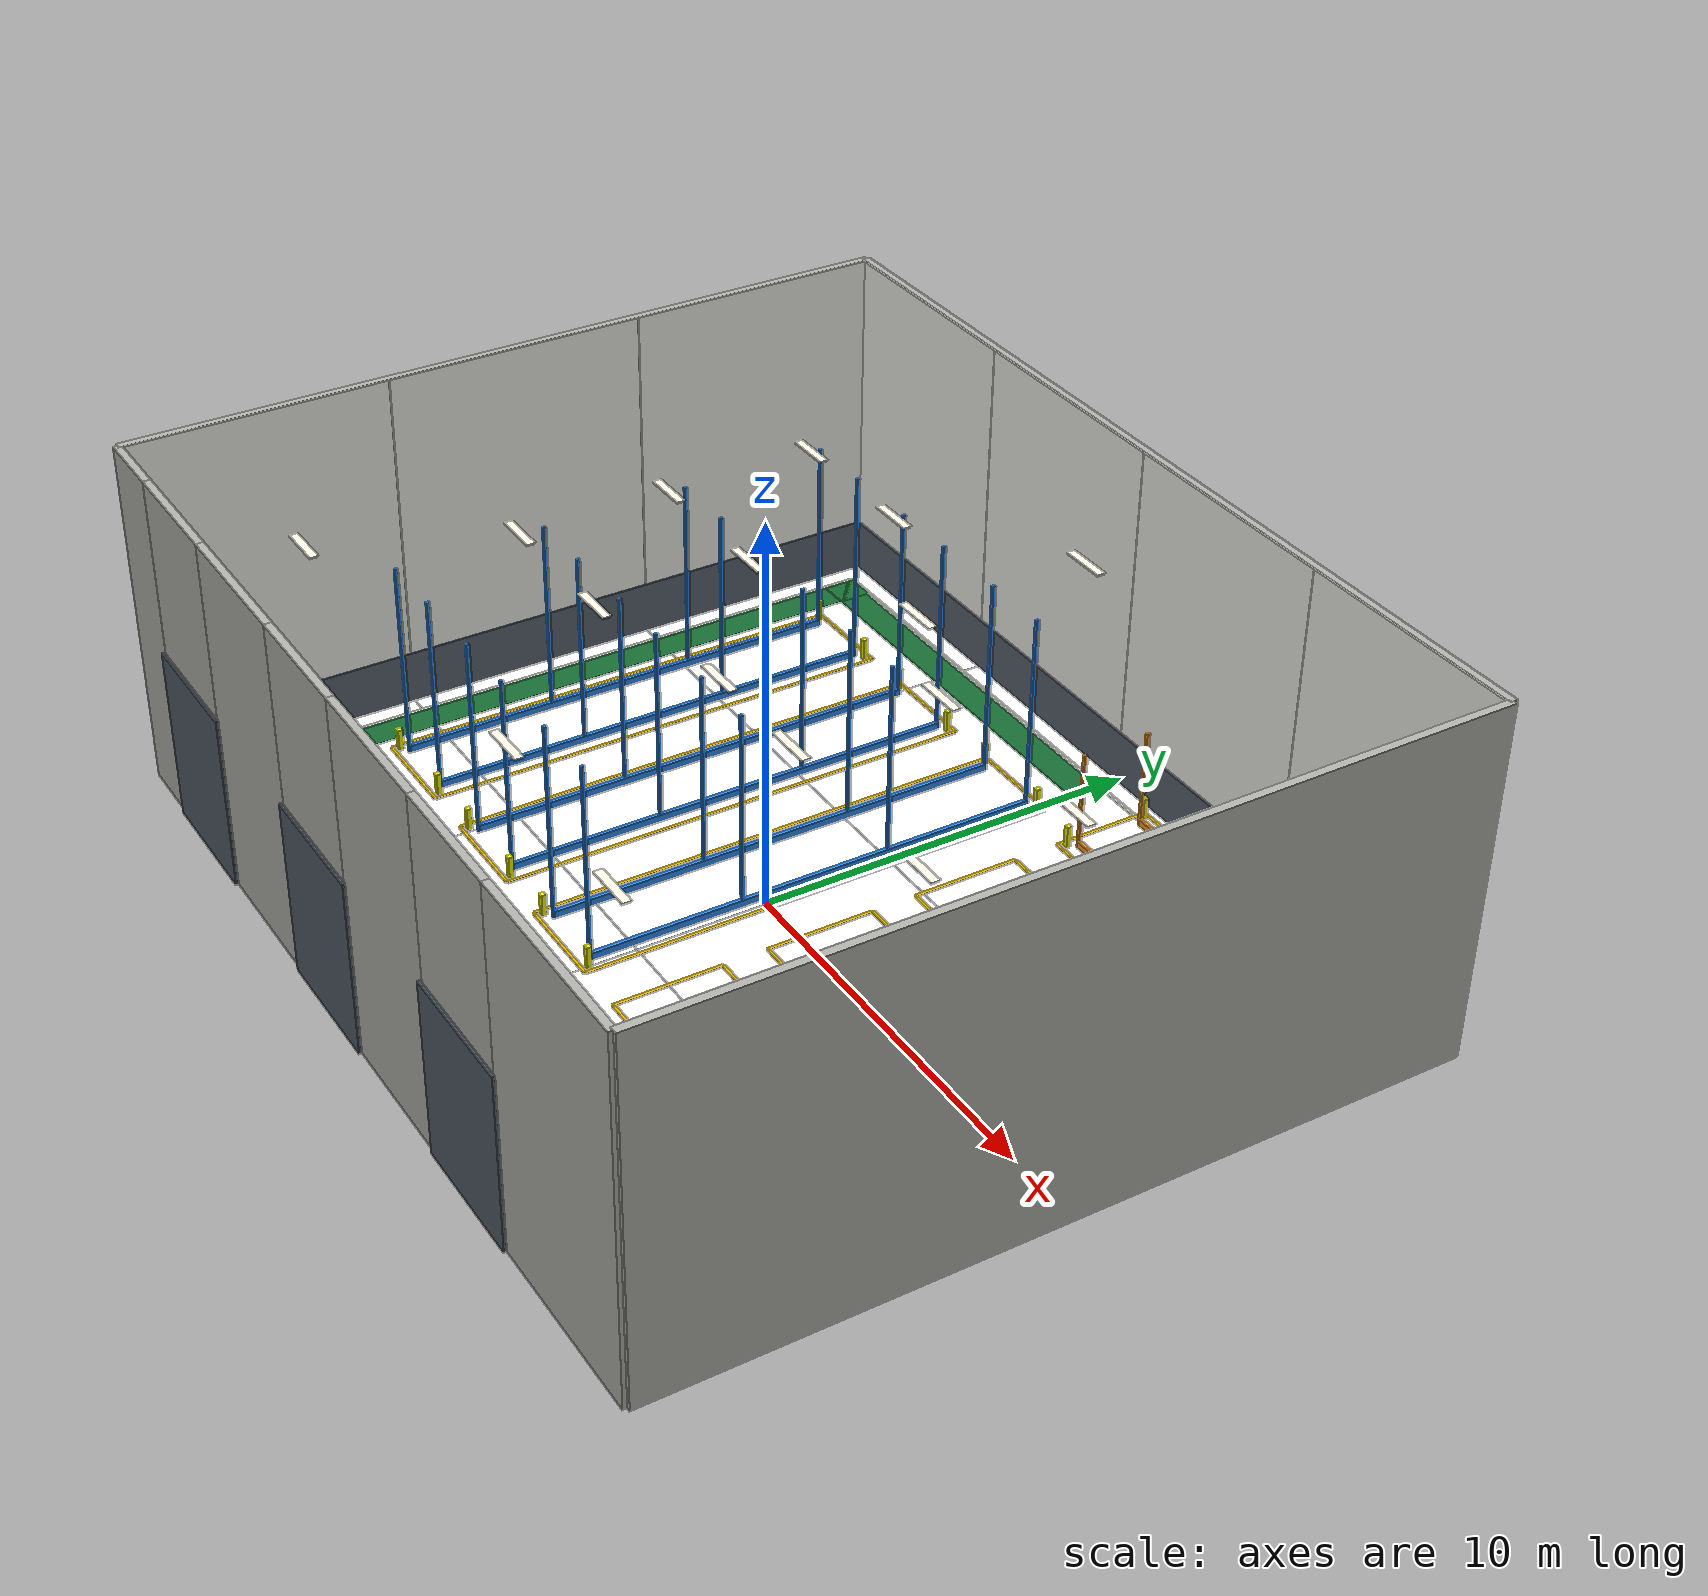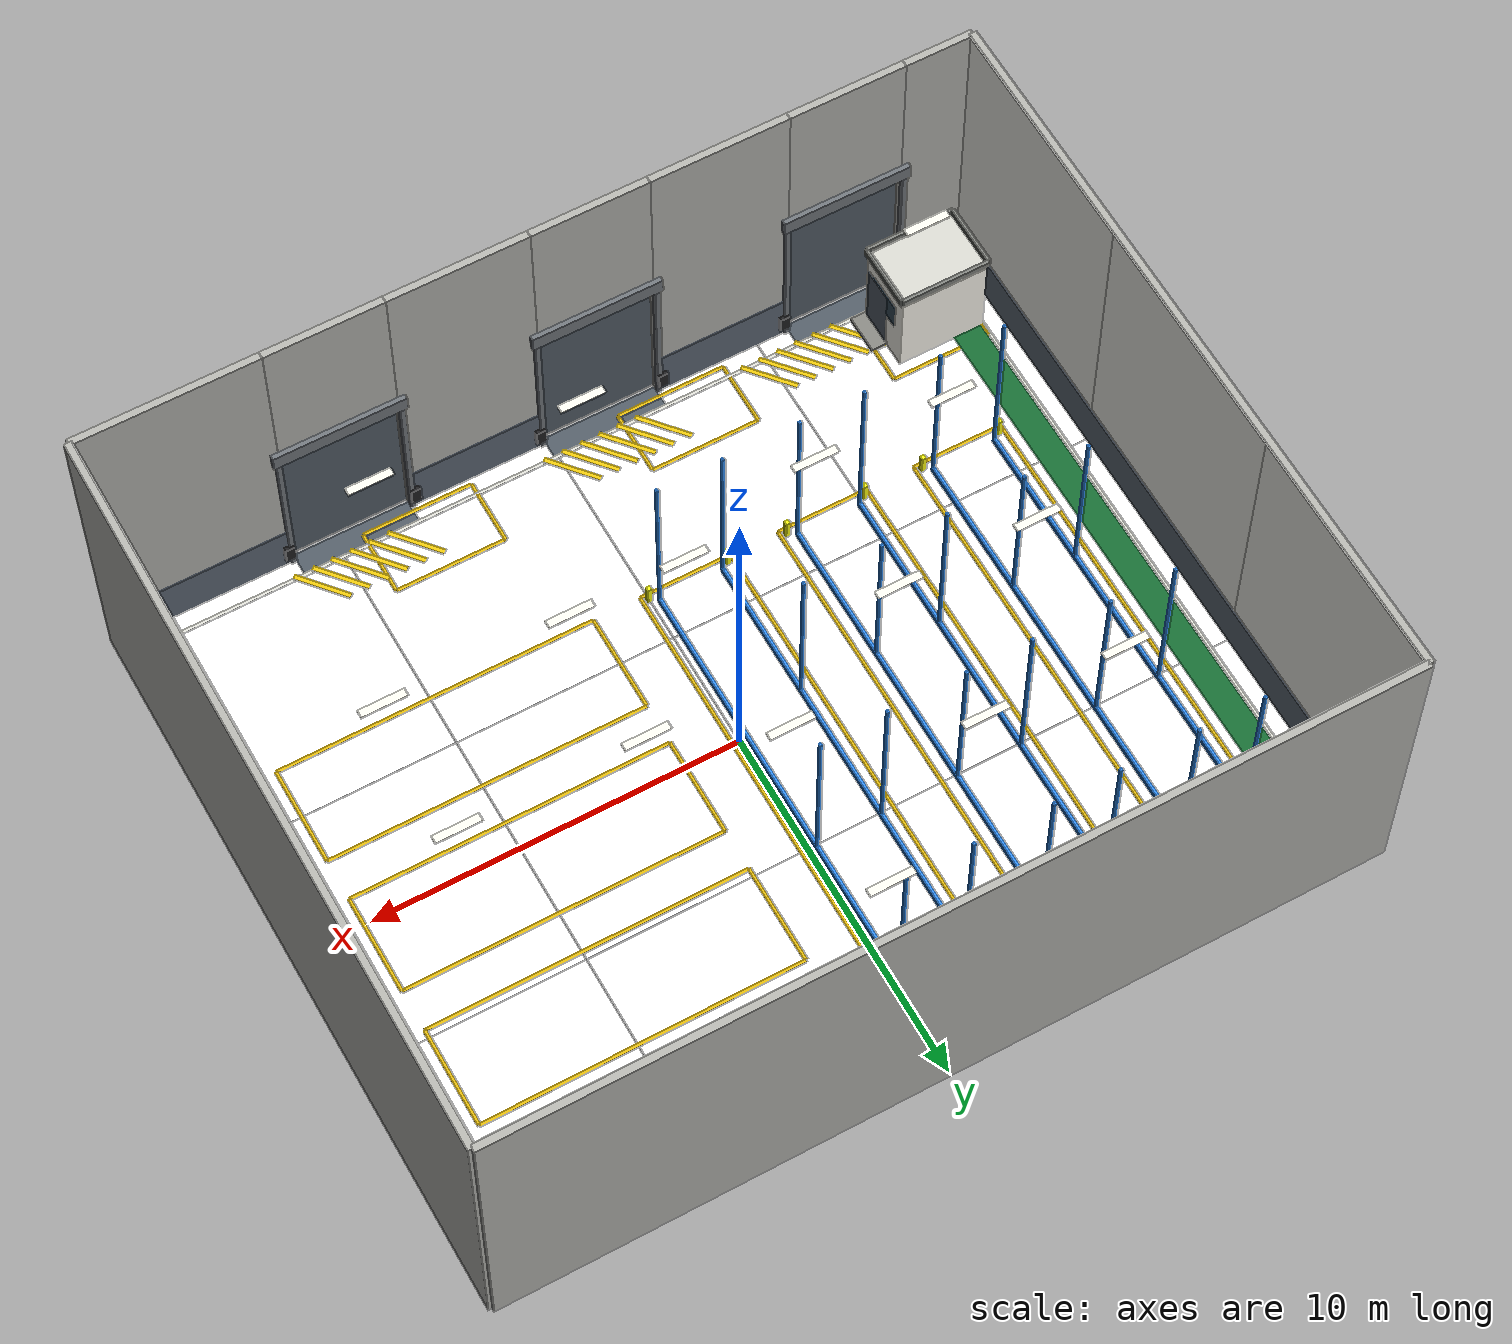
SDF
<sdf version="1.8">
 <world name="warehouse_v2">
  <physics name="default_physics" type="ode">
   <max_step_size>0.001</max_step_size>
   <real_time_factor>1.0</real_time_factor>
   <real_time_update_rate>1000</real_time_update_rate>
  </physics>
  <plugin name="gz::sim::systems::Physics" filename="gz-sim-physics-system"/>
  <plugin name="gz::sim::systems::UserCommands" filename="gz-sim-user-commands-system"/>
  <plugin name="gz::sim::systems::SceneBroadcaster" filename="gz-sim-scene-broadcaster-system"/>
  <plugin name="gz::sim::systems::Contact" filename="gz-sim-contact-system"/>
  <plugin name="gz::sim::systems::Sensors" filename="gz-sim-sensors-system">
   <render_engine>ogre2</render_engine>
  </plugin>
  <gravity>0 0 -9.81</gravity>
  <magnetic_field>6e-06 2.3e-05 -4.2e-05</magnetic_field>
  <atmosphere type="adiabatic"/>
  <scene>
   <ambient>0.20 0.20 0.21 1</ambient>
   <background>0.74 0.78 0.82 1</background>
   <shadows>false</shadows>
  </scene>
  <light type="directional" name="sun">
   <pose>0 0 12 0 0 0</pose>
   <cast_shadows>false</cast_shadows>
   <diffuse>0.42 0.41 0.40 1</diffuse>
   <specular>0.12 0.12 0.12 1</specular>
   <direction>-0.35 0.55 -0.80</direction>
   <attenuation>
    <range>60</range>
    <constant>0.9</constant>
    <linear>0.01</linear>
    <quadratic>0.001</quadratic>
   </attenuation>
  </light>
  <model name="lamp_glow_0">
   <static>true</static>
   <pose>-7.05 -2.40 6.97 0 0 0</pose>
   <link name="link">
    <visual name="visual">
     <geometry><box><size>1.20 0.22 0.03</size></box></geometry>
     <material>
      <ambient>1 0.98 0.92 1</ambient>
      <diffuse>1 0.98 0.92 1</diffuse>
      <specular>0.2 0.2 0.2 1</specular>
      <emissive>1 0.97 0.90 1</emissive>
     </material>
     <cast_shadows>false</cast_shadows>
    </visual>
   </link>
  </model>
  <light type="point" name="lamp_light_0">
   <pose>-7.05 -2.40 6.95 0 0 0</pose>
   <cast_shadows>false</cast_shadows>
   <diffuse>0.600 0.586 0.545 1</diffuse>
   <specular>0.05 0.05 0.05 1</specular>
   <attenuation>
    <range>12.0</range>
    <constant>1.00</constant>
    <linear>0.035</linear>
    <quadratic>0.0060</quadratic>
   </attenuation>
  </light>
  <model name="lamp_glow_1">
   <static>true</static>
   <pose>-7.05 1.50 6.97 0 0 0</pose>
   <link name="link">
    <visual name="visual">
     <geometry><box><size>1.20 0.22 0.03</size></box></geometry>
     <material>
      <ambient>1 0.98 0.92 1</ambient>
      <diffuse>1 0.98 0.92 1</diffuse>
      <specular>0.2 0.2 0.2 1</specular>
      <emissive>1 0.97 0.90 1</emissive>
     </material>
     <cast_shadows>false</cast_shadows>
    </visual>
   </link>
  </model>
  <light type="point" name="lamp_light_1">
   <pose>-7.05 1.50 6.95 0 0 0</pose>
   <cast_shadows>false</cast_shadows>
   <diffuse>0.600 0.586 0.545 1</diffuse>
   <specular>0.05 0.05 0.05 1</specular>
   <attenuation>
    <range>12.0</range>
    <constant>1.00</constant>
    <linear>0.035</linear>
    <quadratic>0.0060</quadratic>
   </attenuation>
  </light>
  <model name="lamp_glow_2">
   <static>true</static>
   <pose>-7.05 5.40 6.97 0 0 0</pose>
   <link name="link">
    <visual name="visual">
     <geometry><box><size>1.20 0.22 0.03</size></box></geometry>
     <material>
      <ambient>1 0.98 0.92 1</ambient>
      <diffuse>1 0.98 0.92 1</diffuse>
      <specular>0.2 0.2 0.2 1</specular>
      <emissive>1 0.97 0.90 1</emissive>
     </material>
     <cast_shadows>false</cast_shadows>
    </visual>
   </link>
  </model>
  <light type="point" name="lamp_light_2">
   <pose>-7.05 5.40 6.95 0 0 0</pose>
   <cast_shadows>false</cast_shadows>
   <diffuse>0.600 0.586 0.545 1</diffuse>
   <specular>0.05 0.05 0.05 1</specular>
   <attenuation>
    <range>12.0</range>
    <constant>1.00</constant>
    <linear>0.035</linear>
    <quadratic>0.0060</quadratic>
   </attenuation>
  </light>
  <model name="lamp_glow_3">
   <static>true</static>
   <pose>-3.35 -2.40 6.97 0 0 0</pose>
   <link name="link">
    <visual name="visual">
     <geometry><box><size>1.20 0.22 0.03</size></box></geometry>
     <material>
      <ambient>1 0.98 0.92 1</ambient>
      <diffuse>1 0.98 0.92 1</diffuse>
      <specular>0.2 0.2 0.2 1</specular>
      <emissive>1 0.97 0.90 1</emissive>
     </material>
     <cast_shadows>false</cast_shadows>
    </visual>
   </link>
  </model>
  <light type="point" name="lamp_light_3">
   <pose>-3.35 -2.40 6.95 0 0 0</pose>
   <cast_shadows>false</cast_shadows>
   <diffuse>0.600 0.586 0.545 1</diffuse>
   <specular>0.05 0.05 0.05 1</specular>
   <attenuation>
    <range>12.0</range>
    <constant>1.00</constant>
    <linear>0.035</linear>
    <quadratic>0.0060</quadratic>
   </attenuation>
  </light>
  <model name="lamp_glow_4">
   <static>true</static>
   <pose>-3.35 1.50 6.97 0 0 0</pose>
   <link name="link">
    <visual name="visual">
     <geometry><box><size>1.20 0.22 0.03</size></box></geometry>
     <material>
      <ambient>1 0.98 0.92 1</ambient>
      <diffuse>1 0.98 0.92 1</diffuse>
      <specular>0.2 0.2 0.2 1</specular>
      <emissive>1 0.97 0.90 1</emissive>
     </material>
     <cast_shadows>false</cast_shadows>
    </visual>
   </link>
  </model>
  <light type="point" name="lamp_light_4">
   <pose>-3.35 1.50 6.95 0 0 0</pose>
   <cast_shadows>false</cast_shadows>
   <diffuse>0.600 0.586 0.545 1</diffuse>
   <specular>0.05 0.05 0.05 1</specular>
   <attenuation>
    <range>12.0</range>
    <constant>1.00</constant>
    <linear>0.035</linear>
    <quadratic>0.0060</quadratic>
   </attenuation>
  </light>
  <model name="lamp_glow_5">
   <static>true</static>
   <pose>-3.35 5.40 6.97 0 0 0</pose>
   <link name="link">
    <visual name="visual">
     <geometry><box><size>1.20 0.22 0.03</size></box></geometry>
     <material>
      <ambient>1 0.98 0.92 1</ambient>
      <diffuse>1 0.98 0.92 1</diffuse>
      <specular>0.2 0.2 0.2 1</specular>
      <emissive>1 0.97 0.90 1</emissive>
     </material>
     <cast_shadows>false</cast_shadows>
    </visual>
   </link>
  </model>
  <light type="point" name="lamp_light_5">
   <pose>-3.35 5.40 6.95 0 0 0</pose>
   <cast_shadows>false</cast_shadows>
   <diffuse>0.600 0.586 0.545 1</diffuse>
   <specular>0.05 0.05 0.05 1</specular>
   <attenuation>
    <range>12.0</range>
    <constant>1.00</constant>
    <linear>0.035</linear>
    <quadratic>0.0060</quadratic>
   </attenuation>
  </light>
  <model name="lamp_glow_6">
   <static>true</static>
   <pose>0.62 -6.50 6.97 0 0 0</pose>
   <link name="link">
    <visual name="visual">
     <geometry><box><size>1.20 0.22 0.03</size></box></geometry>
     <material>
      <ambient>1 0.98 0.92 1</ambient>
      <diffuse>1 0.98 0.92 1</diffuse>
      <specular>0.2 0.2 0.2 1</specular>
      <emissive>1 0.97 0.90 1</emissive>
     </material>
     <cast_shadows>false</cast_shadows>
    </visual>
   </link>
  </model>
  <light type="point" name="lamp_light_6">
   <pose>0.62 -6.50 6.95 0 0 0</pose>
   <cast_shadows>false</cast_shadows>
   <diffuse>0.600 0.586 0.545 1</diffuse>
   <specular>0.05 0.05 0.05 1</specular>
   <attenuation>
    <range>12.0</range>
    <constant>1.00</constant>
    <linear>0.035</linear>
    <quadratic>0.0060</quadratic>
   </attenuation>
  </light>
  <model name="lamp_glow_7">
   <static>true</static>
   <pose>0.62 -1.50 6.97 0 0 0</pose>
   <link name="link">
    <visual name="visual">
     <geometry><box><size>1.20 0.22 0.03</size></box></geometry>
     <material>
      <ambient>1 0.98 0.92 1</ambient>
      <diffuse>1 0.98 0.92 1</diffuse>
      <specular>0.2 0.2 0.2 1</specular>
      <emissive>1 0.97 0.90 1</emissive>
     </material>
     <cast_shadows>false</cast_shadows>
    </visual>
   </link>
  </model>
  <light type="point" name="lamp_light_7">
   <pose>0.62 -1.50 6.95 0 0 0</pose>
   <cast_shadows>false</cast_shadows>
   <diffuse>0.600 0.586 0.545 1</diffuse>
   <specular>0.05 0.05 0.05 1</specular>
   <attenuation>
    <range>12.0</range>
    <constant>1.00</constant>
    <linear>0.035</linear>
    <quadratic>0.0060</quadratic>
   </attenuation>
  </light>
  <model name="lamp_glow_8">
   <static>true</static>
   <pose>0.62 3.50 6.97 0 0 0</pose>
   <link name="link">
    <visual name="visual">
     <geometry><box><size>1.20 0.22 0.03</size></box></geometry>
     <material>
      <ambient>1 0.98 0.92 1</ambient>
      <diffuse>1 0.98 0.92 1</diffuse>
      <specular>0.2 0.2 0.2 1</specular>
      <emissive>1 0.97 0.90 1</emissive>
     </material>
     <cast_shadows>false</cast_shadows>
    </visual>
   </link>
  </model>
  <light type="point" name="lamp_light_8">
   <pose>0.62 3.50 6.95 0 0 0</pose>
   <cast_shadows>false</cast_shadows>
   <diffuse>0.600 0.586 0.545 1</diffuse>
   <specular>0.05 0.05 0.05 1</specular>
   <attenuation>
    <range>12.0</range>
    <constant>1.00</constant>
    <linear>0.035</linear>
    <quadratic>0.0060</quadratic>
   </attenuation>
  </light>
  <model name="lamp_glow_9">
   <static>true</static>
   <pose>0.62 8.00 6.97 0 0 0</pose>
   <link name="link">
    <visual name="visual">
     <geometry><box><size>1.20 0.22 0.03</size></box></geometry>
     <material>
      <ambient>1 0.98 0.92 1</ambient>
      <diffuse>1 0.98 0.92 1</diffuse>
      <specular>0.2 0.2 0.2 1</specular>
      <emissive>1 0.97 0.90 1</emissive>
     </material>
     <cast_shadows>false</cast_shadows>
    </visual>
   </link>
  </model>
  <light type="point" name="lamp_light_9">
   <pose>0.62 8.00 6.95 0 0 0</pose>
   <cast_shadows>false</cast_shadows>
   <diffuse>0.600 0.586 0.545 1</diffuse>
   <specular>0.05 0.05 0.05 1</specular>
   <attenuation>
    <range>12.0</range>
    <constant>1.00</constant>
    <linear>0.035</linear>
    <quadratic>0.0060</quadratic>
   </attenuation>
  </light>
  <model name="lamp_glow_10">
   <static>true</static>
   <pose>3.60 -1.50 6.97 0 0 0</pose>
   <link name="link">
    <visual name="visual">
     <geometry><box><size>1.20 0.22 0.03</size></box></geometry>
     <material>
      <ambient>1 0.98 0.92 1</ambient>
      <diffuse>1 0.98 0.92 1</diffuse>
      <specular>0.2 0.2 0.2 1</specular>
      <emissive>1 0.97 0.90 1</emissive>
     </material>
     <cast_shadows>false</cast_shadows>
    </visual>
   </link>
  </model>
  <light type="point" name="lamp_light_10">
   <pose>3.60 -1.50 6.95 0 0 0</pose>
   <cast_shadows>false</cast_shadows>
   <diffuse>0.600 0.586 0.545 1</diffuse>
   <specular>0.05 0.05 0.05 1</specular>
   <attenuation>
    <range>12.0</range>
    <constant>1.00</constant>
    <linear>0.035</linear>
    <quadratic>0.0060</quadratic>
   </attenuation>
  </light>
  <model name="lamp_glow_11">
   <static>true</static>
   <pose>8.40 -1.50 6.97 0 0 0</pose>
   <link name="link">
    <visual name="visual">
     <geometry><box><size>1.20 0.22 0.03</size></box></geometry>
     <material>
      <ambient>1 0.98 0.92 1</ambient>
      <diffuse>1 0.98 0.92 1</diffuse>
      <specular>0.2 0.2 0.2 1</specular>
      <emissive>1 0.97 0.90 1</emissive>
     </material>
     <cast_shadows>false</cast_shadows>
    </visual>
   </link>
  </model>
  <light type="point" name="lamp_light_11">
   <pose>8.40 -1.50 6.95 0 0 0</pose>
   <cast_shadows>false</cast_shadows>
   <diffuse>0.600 0.586 0.545 1</diffuse>
   <specular>0.05 0.05 0.05 1</specular>
   <attenuation>
    <range>12.0</range>
    <constant>1.00</constant>
    <linear>0.035</linear>
    <quadratic>0.0060</quadratic>
   </attenuation>
  </light>
  <model name="lamp_glow_12">
   <static>true</static>
   <pose>3.60 2.15 6.97 0 0 0</pose>
   <link name="link">
    <visual name="visual">
     <geometry><box><size>1.20 0.22 0.03</size></box></geometry>
     <material>
      <ambient>1 0.98 0.92 1</ambient>
      <diffuse>1 0.98 0.92 1</diffuse>
      <specular>0.2 0.2 0.2 1</specular>
      <emissive>1 0.97 0.90 1</emissive>
     </material>
     <cast_shadows>false</cast_shadows>
    </visual>
   </link>
  </model>
  <light type="point" name="lamp_light_12">
   <pose>3.60 2.15 6.95 0 0 0</pose>
   <cast_shadows>false</cast_shadows>
   <diffuse>0.600 0.586 0.545 1</diffuse>
   <specular>0.05 0.05 0.05 1</specular>
   <attenuation>
    <range>12.0</range>
    <constant>1.00</constant>
    <linear>0.035</linear>
    <quadratic>0.0060</quadratic>
   </attenuation>
  </light>
  <model name="lamp_glow_13">
   <static>true</static>
   <pose>8.40 2.15 6.97 0 0 0</pose>
   <link name="link">
    <visual name="visual">
     <geometry><box><size>1.20 0.22 0.03</size></box></geometry>
     <material>
      <ambient>1 0.98 0.92 1</ambient>
      <diffuse>1 0.98 0.92 1</diffuse>
      <specular>0.2 0.2 0.2 1</specular>
      <emissive>1 0.97 0.90 1</emissive>
     </material>
     <cast_shadows>false</cast_shadows>
    </visual>
   </link>
  </model>
  <light type="point" name="lamp_light_13">
   <pose>8.40 2.15 6.95 0 0 0</pose>
   <cast_shadows>false</cast_shadows>
   <diffuse>0.600 0.586 0.545 1</diffuse>
   <specular>0.05 0.05 0.05 1</specular>
   <attenuation>
    <range>12.0</range>
    <constant>1.00</constant>
    <linear>0.035</linear>
    <quadratic>0.0060</quadratic>
   </attenuation>
  </light>
  <model name="lamp_glow_14">
   <static>true</static>
   <pose>-9.00 -6.90 6.97 0 0 0</pose>
   <link name="link">
    <visual name="visual">
     <geometry><box><size>1.20 0.22 0.03</size></box></geometry>
     <material>
      <ambient>1 0.98 0.92 1</ambient>
      <diffuse>1 0.98 0.92 1</diffuse>
      <specular>0.2 0.2 0.2 1</specular>
      <emissive>1 0.97 0.90 1</emissive>
     </material>
     <cast_shadows>false</cast_shadows>
    </visual>
   </link>
  </model>
  <light type="point" name="lamp_light_14">
   <pose>-9.00 -6.90 6.95 0 0 0</pose>
   <cast_shadows>false</cast_shadows>
   <diffuse>0.600 0.586 0.545 1</diffuse>
   <specular>0.05 0.05 0.05 1</specular>
   <attenuation>
    <range>12.0</range>
    <constant>1.00</constant>
    <linear>0.035</linear>
    <quadratic>0.0060</quadratic>
   </attenuation>
  </light>
  <model name="lamp_glow_15">
   <static>true</static>
   <pose>6.00 -6.90 6.97 0 0 0</pose>
   <link name="link">
    <visual name="visual">
     <geometry><box><size>1.20 0.22 0.03</size></box></geometry>
     <material>
      <ambient>1 0.98 0.92 1</ambient>
      <diffuse>1 0.98 0.92 1</diffuse>
      <specular>0.2 0.2 0.2 1</specular>
      <emissive>1 0.97 0.90 1</emissive>
     </material>
     <cast_shadows>false</cast_shadows>
    </visual>
   </link>
  </model>
  <light type="point" name="lamp_light_15">
   <pose>6.00 -6.90 6.95 0 0 0</pose>
   <cast_shadows>false</cast_shadows>
   <diffuse>0.600 0.586 0.545 1</diffuse>
   <specular>0.05 0.05 0.05 1</specular>
   <attenuation>
    <range>12.0</range>
    <constant>1.00</constant>
    <linear>0.035</linear>
    <quadratic>0.0060</quadratic>
   </attenuation>
  </light>
  <model name="ground_plane">
   <static>true</static>
   <link name="link">
    <collision name="collision">
     <geometry><plane><normal>0 0 1</normal><size>24.5 20.5</size></plane></geometry>
    </collision>
   </link>
  </model>
  <model name="warehouse_v2_floor">
   <static>true</static>
   <link name="floor_bay_0_0">
    <pose>-9.000 -6.667 0.005 0 0 0.0000</pose>
    <visual name="visual">
     <geometry><box><size>5.985 6.652 0.010</size></box></geometry>
     <material>
      <ambient>1 1 1 1</ambient>
      <diffuse>1 1 1 1</diffuse>
      <specular>0.08 0.08 0.08 1</specular>
      <pbr>
       <metal>
        <albedo_map>model://warehouse_pbr/materials/textures/concrete_albedo.png</albedo_map>
        <normal_map>model://warehouse_pbr/materials/textures/concrete_normal.png</normal_map>
        <roughness_map>model://warehouse_pbr/materials/textures/concrete_roughness.png</roughness_map>
        <metalness>0.0</metalness>
       </metal>
      </pbr>
     </material>
    </visual>
   </link>
   <link name="floor_bay_0_1">
    <pose>-9.000 0.000 0.005 0 0 0.0000</pose>
    <visual name="visual">
     <geometry><box><size>5.985 6.652 0.010</size></box></geometry>
     <material>
      <ambient>1 1 1 1</ambient>
      <diffuse>1 1 1 1</diffuse>
      <specular>0.08 0.08 0.08 1</specular>
      <pbr>
       <metal>
        <albedo_map>model://warehouse_pbr/materials/textures/concrete_albedo.png</albedo_map>
        <normal_map>model://warehouse_pbr/materials/textures/concrete_normal.png</normal_map>
        <roughness_map>model://warehouse_pbr/materials/textures/concrete_roughness.png</roughness_map>
        <metalness>0.0</metalness>
       </metal>
      </pbr>
     </material>
    </visual>
   </link>
   <link name="floor_bay_0_2">
    <pose>-9.000 6.667 0.005 0 0 0.0000</pose>
    <visual name="visual">
     <geometry><box><size>5.985 6.652 0.010</size></box></geometry>
     <material>
      <ambient>1 1 1 1</ambient>
      <diffuse>1 1 1 1</diffuse>
      <specular>0.08 0.08 0.08 1</specular>
      <pbr>
       <metal>
        <albedo_map>model://warehouse_pbr/materials/textures/concrete_albedo.png</albedo_map>
        <normal_map>model://warehouse_pbr/materials/textures/concrete_normal.png</normal_map>
        <roughness_map>model://warehouse_pbr/materials/textures/concrete_roughness.png</roughness_map>
        <metalness>0.0</metalness>
       </metal>
      </pbr>
     </material>
    </visual>
   </link>
   <link name="floor_bay_1_0">
    <pose>-3.000 -6.667 0.005 0 0 0.0000</pose>
    <visual name="visual">
     <geometry><box><size>5.985 6.652 0.010</size></box></geometry>
     <material>
      <ambient>1 1 1 1</ambient>
      <diffuse>1 1 1 1</diffuse>
      <specular>0.08 0.08 0.08 1</specular>
      <pbr>
       <metal>
        <albedo_map>model://warehouse_pbr/materials/textures/concrete_albedo.png</albedo_map>
        <normal_map>model://warehouse_pbr/materials/textures/concrete_normal.png</normal_map>
        <roughness_map>model://warehouse_pbr/materials/textures/concrete_roughness.png</roughness_map>
        <metalness>0.0</metalness>
       </metal>
      </pbr>
     </material>
    </visual>
   </link>
   <link name="floor_bay_1_1">
    <pose>-3.000 0.000 0.005 0 0 0.0000</pose>
    <visual name="visual">
     <geometry><box><size>5.985 6.652 0.010</size></box></geometry>
     <material>
      <ambient>1 1 1 1</ambient>
      <diffuse>1 1 1 1</diffuse>
      <specular>0.08 0.08 0.08 1</specular>
      <pbr>
       <metal>
        <albedo_map>model://warehouse_pbr/materials/textures/concrete_albedo.png</albedo_map>
        <normal_map>model://warehouse_pbr/materials/textures/concrete_normal.png</normal_map>
        <roughness_map>model://warehouse_pbr/materials/textures/concrete_roughness.png</roughness_map>
        <metalness>0.0</metalness>
       </metal>
      </pbr>
     </material>
    </visual>
   </link>
   <link name="floor_bay_1_2">
    <pose>-3.000 6.667 0.005 0 0 0.0000</pose>
    <visual name="visual">
     <geometry><box><size>5.985 6.652 0.010</size></box></geometry>
     <material>
      <ambient>1 1 1 1</ambient>
      <diffuse>1 1 1 1</diffuse>
      <specular>0.08 0.08 0.08 1</specular>
      <pbr>
       <metal>
        <albedo_map>model://warehouse_pbr/materials/textures/concrete_albedo.png</albedo_map>
        <normal_map>model://warehouse_pbr/materials/textures/concrete_normal.png</normal_map>
        <roughness_map>model://warehouse_pbr/materials/textures/concrete_roughness.png</roughness_map>
        <metalness>0.0</metalness>
       </metal>
      </pbr>
     </material>
    </visual>
   </link>
   <link name="floor_bay_2_0">
    <pose>3.000 -6.667 0.005 0 0 0.0000</pose>
    <visual name="visual">
     <geometry><box><size>5.985 6.652 0.010</size></box></geometry>
     <material>
      <ambient>1 1 1 1</ambient>
      <diffuse>1 1 1 1</diffuse>
      <specular>0.08 0.08 0.08 1</specular>
      <pbr>
       <metal>
        <albedo_map>model://warehouse_pbr/materials/textures/concrete_albedo.png</albedo_map>
        <normal_map>model://warehouse_pbr/materials/textures/concrete_normal.png</normal_map>
        <roughness_map>model://warehouse_pbr/materials/textures/concrete_roughness.png</roughness_map>
        <metalness>0.0</metalness>
       </metal>
      </pbr>
     </material>
    </visual>
   </link>
   <link name="floor_bay_2_1">
    <pose>3.000 0.000 0.005 0 0 0.0000</pose>
    <visual name="visual">
     <geometry><box><size>5.985 6.652 0.010</size></box></geometry>
     <material>
      <ambient>1 1 1 1</ambient>
      <diffuse>1 1 1 1</diffuse>
      <specular>0.08 0.08 0.08 1</specular>
      <pbr>
       <metal>
        <albedo_map>model://warehouse_pbr/materials/textures/concrete_albedo.png</albedo_map>
        <normal_map>model://warehouse_pbr/materials/textures/concrete_normal.png</normal_map>
        <roughness_map>model://warehouse_pbr/materials/textures/concrete_roughness.png</roughness_map>
        <metalness>0.0</metalness>
       </metal>
      </pbr>
     </material>
    </visual>
   </link>
   <link name="floor_bay_2_2">
    <pose>3.000 6.667 0.005 0 0 0.0000</pose>
    <visual name="visual">
     <geometry><box><size>5.985 6.652 0.010</size></box></geometry>
     <material>
      <ambient>1 1 1 1</ambient>
      <diffuse>1 1 1 1</diffuse>
      <specular>0.08 0.08 0.08 1</specular>
      <pbr>
       <metal>
        <albedo_map>model://warehouse_pbr/materials/textures/concrete_albedo.png</albedo_map>
        <normal_map>model://warehouse_pbr/materials/textures/concrete_normal.png</normal_map>
        <roughness_map>model://warehouse_pbr/materials/textures/concrete_roughness.png</roughness_map>
        <metalness>0.0</metalness>
       </metal>
      </pbr>
     </material>
    </visual>
   </link>
   <link name="floor_bay_3_0">
    <pose>9.000 -6.667 0.005 0 0 0.0000</pose>
    <visual name="visual">
     <geometry><box><size>5.985 6.652 0.010</size></box></geometry>
     <material>
      <ambient>1 1 1 1</ambient>
      <diffuse>1 1 1 1</diffuse>
      <specular>0.08 0.08 0.08 1</specular>
      <pbr>
       <metal>
        <albedo_map>model://warehouse_pbr/materials/textures/concrete_albedo.png</albedo_map>
        <normal_map>model://warehouse_pbr/materials/textures/concrete_normal.png</normal_map>
        <roughness_map>model://warehouse_pbr/materials/textures/concrete_roughness.png</roughness_map>
        <metalness>0.0</metalness>
       </metal>
      </pbr>
     </material>
    </visual>
   </link>
   <link name="floor_bay_3_1">
    <pose>9.000 0.000 0.005 0 0 0.0000</pose>
    <visual name="visual">
     <geometry><box><size>5.985 6.652 0.010</size></box></geometry>
     <material>
      <ambient>1 1 1 1</ambient>
      <diffuse>1 1 1 1</diffuse>
      <specular>0.08 0.08 0.08 1</specular>
      <pbr>
       <metal>
        <albedo_map>model://warehouse_pbr/materials/textures/concrete_albedo.png</albedo_map>
        <normal_map>model://warehouse_pbr/materials/textures/concrete_normal.png</normal_map>
        <roughness_map>model://warehouse_pbr/materials/textures/concrete_roughness.png</roughness_map>
        <metalness>0.0</metalness>
       </metal>
      </pbr>
     </material>
    </visual>
   </link>
   <link name="floor_bay_3_2">
    <pose>9.000 6.667 0.005 0 0 0.0000</pose>
    <visual name="visual">
     <geometry><box><size>5.985 6.652 0.010</size></box></geometry>
     <material>
      <ambient>1 1 1 1</ambient>
      <diffuse>1 1 1 1</diffuse>
      <specular>0.08 0.08 0.08 1</specular>
      <pbr>
       <metal>
        <albedo_map>model://warehouse_pbr/materials/textures/concrete_albedo.png</albedo_map>
        <normal_map>model://warehouse_pbr/materials/textures/concrete_normal.png</normal_map>
        <roughness_map>model://warehouse_pbr/materials/textures/concrete_roughness.png</roughness_map>
        <metalness>0.0</metalness>
       </metal>
      </pbr>
     </material>
    </visual>
   </link>
  </model>
  <model name="warehouse_v2_wall_lining">
   <static>true</static>
   <link name="panel_n_0">
    <pose>-9.000 9.890 4.500 0 0 0.0000</pose>
    <visual name="visual">
     <geometry><box><size>5.980 0.020 8.980</size></box></geometry>
     <material>
      <ambient>0.97 0.97 0.94 1</ambient>
      <diffuse>0.97 0.97 0.94 1</diffuse>
      <specular>0.08 0.08 0.08 1</specular>
      <pbr>
       <metal>
        <albedo_map>model://warehouse_pbr/materials/textures/concrete_albedo.png</albedo_map>
        <normal_map>model://warehouse_pbr/materials/textures/concrete_normal.png</normal_map>
        <roughness_map>model://warehouse_pbr/materials/textures/concrete_roughness.png</roughness_map>
        <metalness>0.0</metalness>
       </metal>
      </pbr>
     </material>
    </visual>
   </link>
   <link name="panel_n_1">
    <pose>-3.000 9.890 4.500 0 0 0.0000</pose>
    <visual name="visual">
     <geometry><box><size>5.980 0.020 8.980</size></box></geometry>
     <material>
      <ambient>0.97 0.97 0.94 1</ambient>
      <diffuse>0.97 0.97 0.94 1</diffuse>
      <specular>0.08 0.08 0.08 1</specular>
      <pbr>
       <metal>
        <albedo_map>model://warehouse_pbr/materials/textures/concrete_albedo.png</albedo_map>
        <normal_map>model://warehouse_pbr/materials/textures/concrete_normal.png</normal_map>
        <roughness_map>model://warehouse_pbr/materials/textures/concrete_roughness.png</roughness_map>
        <metalness>0.0</metalness>
       </metal>
      </pbr>
     </material>
    </visual>
   </link>
   <link name="panel_n_2">
    <pose>3.000 9.890 4.500 0 0 0.0000</pose>
    <visual name="visual">
     <geometry><box><size>5.980 0.020 8.980</size></box></geometry>
     <material>
      <ambient>0.97 0.97 0.94 1</ambient>
      <diffuse>0.97 0.97 0.94 1</diffuse>
      <specular>0.08 0.08 0.08 1</specular>
      <pbr>
       <metal>
        <albedo_map>model://warehouse_pbr/materials/textures/concrete_albedo.png</albedo_map>
        <normal_map>model://warehouse_pbr/materials/textures/concrete_normal.png</normal_map>
        <roughness_map>model://warehouse_pbr/materials/textures/concrete_roughness.png</roughness_map>
        <metalness>0.0</metalness>
       </metal>
      </pbr>
     </material>
    </visual>
   </link>
   <link name="panel_n_3">
    <pose>9.000 9.890 4.500 0 0 0.0000</pose>
    <visual name="visual">
     <geometry><box><size>5.980 0.020 8.980</size></box></geometry>
     <material>
      <ambient>0.97 0.97 0.94 1</ambient>
      <diffuse>0.97 0.97 0.94 1</diffuse>
      <specular>0.08 0.08 0.08 1</specular>
      <pbr>
       <metal>
        <albedo_map>model://warehouse_pbr/materials/textures/concrete_albedo.png</albedo_map>
        <normal_map>model://warehouse_pbr/materials/textures/concrete_normal.png</normal_map>
        <roughness_map>model://warehouse_pbr/materials/textures/concrete_roughness.png</roughness_map>
        <metalness>0.0</metalness>
       </metal>
      </pbr>
     </material>
    </visual>
   </link>
   <link name="panel_w_0">
    <pose>-11.890 -6.667 4.500 0 0 0.0000</pose>
    <visual name="visual">
     <geometry><box><size>0.020 6.647 8.980</size></box></geometry>
     <material>
      <ambient>0.97 0.97 0.94 1</ambient>
      <diffuse>0.97 0.97 0.94 1</diffuse>
      <specular>0.08 0.08 0.08 1</specular>
      <pbr>
       <metal>
        <albedo_map>model://warehouse_pbr/materials/textures/concrete_albedo.png</albedo_map>
        <normal_map>model://warehouse_pbr/materials/textures/concrete_normal.png</normal_map>
        <roughness_map>model://warehouse_pbr/materials/textures/concrete_roughness.png</roughness_map>
        <metalness>0.0</metalness>
       </metal>
      </pbr>
     </material>
    </visual>
   </link>
   <link name="panel_e_0">
    <pose>11.890 -6.667 4.500 0 0 0.0000</pose>
    <visual name="visual">
     <geometry><box><size>0.020 6.647 8.980</size></box></geometry>
     <material>
      <ambient>0.97 0.97 0.94 1</ambient>
      <diffuse>0.97 0.97 0.94 1</diffuse>
      <specular>0.08 0.08 0.08 1</specular>
      <pbr>
       <metal>
        <albedo_map>model://warehouse_pbr/materials/textures/concrete_albedo.png</albedo_map>
        <normal_map>model://warehouse_pbr/materials/textures/concrete_normal.png</normal_map>
        <roughness_map>model://warehouse_pbr/materials/textures/concrete_roughness.png</roughness_map>
        <metalness>0.0</metalness>
       </metal>
      </pbr>
     </material>
    </visual>
   </link>
   <link name="panel_w_1">
    <pose>-11.890 0.000 4.500 0 0 0.0000</pose>
    <visual name="visual">
     <geometry><box><size>0.020 6.647 8.980</size></box></geometry>
     <material>
      <ambient>0.97 0.97 0.94 1</ambient>
      <diffuse>0.97 0.97 0.94 1</diffuse>
      <specular>0.08 0.08 0.08 1</specular>
      <pbr>
       <metal>
        <albedo_map>model://warehouse_pbr/materials/textures/concrete_albedo.png</albedo_map>
        <normal_map>model://warehouse_pbr/materials/textures/concrete_normal.png</normal_map>
        <roughness_map>model://warehouse_pbr/materials/textures/concrete_roughness.png</roughness_map>
        <metalness>0.0</metalness>
       </metal>
      </pbr>
     </material>
    </visual>
   </link>
   <link name="panel_e_1">
    <pose>11.890 0.000 4.500 0 0 0.0000</pose>
    <visual name="visual">
     <geometry><box><size>0.020 6.647 8.980</size></box></geometry>
     <material>
      <ambient>0.97 0.97 0.94 1</ambient>
      <diffuse>0.97 0.97 0.94 1</diffuse>
      <specular>0.08 0.08 0.08 1</specular>
      <pbr>
       <metal>
        <albedo_map>model://warehouse_pbr/materials/textures/concrete_albedo.png</albedo_map>
        <normal_map>model://warehouse_pbr/materials/textures/concrete_normal.png</normal_map>
        <roughness_map>model://warehouse_pbr/materials/textures/concrete_roughness.png</roughness_map>
        <metalness>0.0</metalness>
       </metal>
      </pbr>
     </material>
    </visual>
   </link>
   <link name="panel_w_2">
    <pose>-11.890 6.667 4.500 0 0 0.0000</pose>
    <visual name="visual">
     <geometry><box><size>0.020 6.647 8.980</size></box></geometry>
     <material>
      <ambient>0.97 0.97 0.94 1</ambient>
      <diffuse>0.97 0.97 0.94 1</diffuse>
      <specular>0.08 0.08 0.08 1</specular>
      <pbr>
       <metal>
        <albedo_map>model://warehouse_pbr/materials/textures/concrete_albedo.png</albedo_map>
        <normal_map>model://warehouse_pbr/materials/textures/concrete_normal.png</normal_map>
        <roughness_map>model://warehouse_pbr/materials/textures/concrete_roughness.png</roughness_map>
        <metalness>0.0</metalness>
       </metal>
      </pbr>
     </material>
    </visual>
   </link>
   <link name="panel_e_2">
    <pose>11.890 6.667 4.500 0 0 0.0000</pose>
    <visual name="visual">
     <geometry><box><size>0.020 6.647 8.980</size></box></geometry>
     <material>
      <ambient>0.97 0.97 0.94 1</ambient>
      <diffuse>0.97 0.97 0.94 1</diffuse>
      <specular>0.08 0.08 0.08 1</specular>
      <pbr>
       <metal>
        <albedo_map>model://warehouse_pbr/materials/textures/concrete_albedo.png</albedo_map>
        <normal_map>model://warehouse_pbr/materials/textures/concrete_normal.png</normal_map>
        <roughness_map>model://warehouse_pbr/materials/textures/concrete_roughness.png</roughness_map>
        <metalness>0.0</metalness>
       </metal>
      </pbr>
     </material>
    </visual>
   </link>
  </model>
  <model name="warehouse_shell">
   <static>true</static>
   <link name="wall_east">
    <pose>12.000 0.000 4.500 0 0 0.0000</pose>
    <collision name="collision"><geometry><box><size>0.200 20.000 9.000</size></box></geometry></collision>
    <sensor name="contact" type="contact">
     <contact><collision>collision</collision></contact>
     <update_rate>20</update_rate>
    </sensor>
    <visual name="visual">
     <geometry><box><size>0.200 20.000 9.000</size></box></geometry>
     <material>
      <ambient>0.70 0.70 0.68 1</ambient>
      <diffuse>0.70 0.70 0.68 1</diffuse>
      <specular>0.100 0.100 0.100 1</specular>
      <pbr><metal><metalness>0.00</metalness><roughness>0.80</roughness></metal></pbr>
     </material>
    </visual>
   </link>
   <link name="wall_west">
    <pose>-12.000 0.000 4.500 0 0 0.0000</pose>
    <collision name="collision"><geometry><box><size>0.200 20.000 9.000</size></box></geometry></collision>
    <sensor name="contact" type="contact">
     <contact><collision>collision</collision></contact>
     <update_rate>20</update_rate>
    </sensor>
    <visual name="visual">
     <geometry><box><size>0.200 20.000 9.000</size></box></geometry>
     <material>
      <ambient>0.70 0.70 0.68 1</ambient>
      <diffuse>0.70 0.70 0.68 1</diffuse>
      <specular>0.100 0.100 0.100 1</specular>
      <pbr><metal><metalness>0.00</metalness><roughness>0.80</roughness></metal></pbr>
     </material>
    </visual>
   </link>
   <link name="wall_north">
    <pose>0.000 10.000 4.500 0 0 0.0000</pose>
    <collision name="collision"><geometry><box><size>24.000 0.200 9.000</size></box></geometry></collision>
    <sensor name="contact" type="contact">
     <contact><collision>collision</collision></contact>
     <update_rate>20</update_rate>
    </sensor>
    <visual name="visual">
     <geometry><box><size>24.000 0.200 9.000</size></box></geometry>
     <material>
      <ambient>0.70 0.70 0.68 1</ambient>
      <diffuse>0.70 0.70 0.68 1</diffuse>
      <specular>0.100 0.100 0.100 1</specular>
      <pbr><metal><metalness>0.00</metalness><roughness>0.80</roughness></metal></pbr>
     </material>
    </visual>
   </link>
   <link name="wall_south_0">
    <pose>-11.050 -10.000 4.500 0 0 0.0000</pose>
    <collision name="collision"><geometry><box><size>1.900 0.200 9.000</size></box></geometry></collision>
    <sensor name="contact" type="contact">
     <contact><collision>collision</collision></contact>
     <update_rate>20</update_rate>
    </sensor>
    <visual name="visual">
     <geometry><box><size>1.900 0.200 9.000</size></box></geometry>
     <material>
      <ambient>0.70 0.70 0.68 1</ambient>
      <diffuse>0.70 0.70 0.68 1</diffuse>
      <specular>0.100 0.100 0.100 1</specular>
      <pbr><metal><metalness>0.00</metalness><roughness>0.80</roughness></metal></pbr>
     </material>
    </visual>
   </link>
   <link name="wall_south_1">
    <pose>-5.000 -10.000 4.500 0 0 0.0000</pose>
    <collision name="collision"><geometry><box><size>3.800 0.200 9.000</size></box></geometry></collision>
    <sensor name="contact" type="contact">
     <contact><collision>collision</collision></contact>
     <update_rate>20</update_rate>
    </sensor>
    <visual name="visual">
     <geometry><box><size>3.800 0.200 9.000</size></box></geometry>
     <material>
      <ambient>0.70 0.70 0.68 1</ambient>
      <diffuse>0.70 0.70 0.68 1</diffuse>
      <specular>0.100 0.100 0.100 1</specular>
      <pbr><metal><metalness>0.00</metalness><roughness>0.80</roughness></metal></pbr>
     </material>
    </visual>
   </link>
   <link name="wall_south_2">
    <pose>2.000 -10.000 4.500 0 0 0.0000</pose>
    <collision name="collision"><geometry><box><size>3.800 0.200 9.000</size></box></geometry></collision>
    <sensor name="contact" type="contact">
     <contact><collision>collision</collision></contact>
     <update_rate>20</update_rate>
    </sensor>
    <visual name="visual">
     <geometry><box><size>3.800 0.200 9.000</size></box></geometry>
     <material>
      <ambient>0.70 0.70 0.68 1</ambient>
      <diffuse>0.70 0.70 0.68 1</diffuse>
      <specular>0.100 0.100 0.100 1</specular>
      <pbr><metal><metalness>0.00</metalness><roughness>0.80</roughness></metal></pbr>
     </material>
    </visual>
   </link>
   <link name="wall_south_3">
    <pose>9.550 -10.000 4.500 0 0 0.0000</pose>
    <collision name="collision"><geometry><box><size>4.900 0.200 9.000</size></box></geometry></collision>
    <sensor name="contact" type="contact">
     <contact><collision>collision</collision></contact>
     <update_rate>20</update_rate>
    </sensor>
    <visual name="visual">
     <geometry><box><size>4.900 0.200 9.000</size></box></geometry>
     <material>
      <ambient>0.70 0.70 0.68 1</ambient>
      <diffuse>0.70 0.70 0.68 1</diffuse>
      <specular>0.100 0.100 0.100 1</specular>
      <pbr><metal><metalness>0.00</metalness><roughness>0.80</roughness></metal></pbr>
     </material>
    </visual>
   </link>
   <link name="door_head_0">
    <pose>-8.500 -10.000 6.750 0 0 0.0000</pose>
    <collision name="collision"><geometry><box><size>3.200 0.200 4.500</size></box></geometry></collision>
    <sensor name="contact" type="contact">
     <contact><collision>collision</collision></contact>
     <update_rate>20</update_rate>
    </sensor>
    <visual name="visual">
     <geometry><box><size>3.200 0.200 4.500</size></box></geometry>
     <material>
      <ambient>0.70 0.70 0.68 1</ambient>
      <diffuse>0.70 0.70 0.68 1</diffuse>
      <specular>0.100 0.100 0.100 1</specular>
      <pbr><metal><metalness>0.00</metalness><roughness>0.80</roughness></metal></pbr>
     </material>
    </visual>
   </link>
   <link name="door_frame_0">
    <pose>-8.500 -10.130 2.250 0 0 0.0000</pose>
    <visual name="visual">
     <geometry><box><size>3.360 0.080 4.500</size></box></geometry>
     <material>
      <ambient>0.32 0.36 0.40 1</ambient>
      <diffuse>0.32 0.36 0.40 1</diffuse>
      <specular>0.100 0.100 0.100 1</specular>
      <pbr><metal><metalness>0.00</metalness><roughness>0.80</roughness></metal></pbr>
     </material>
    </visual>
   </link>
   <link name="door_sill_0">
    <pose>-8.500 -9.700 0.008 0 0 0.0000</pose>
    <visual name="visual">
     <geometry><box><size>3.200 0.600 0.014</size></box></geometry>
     <material>
      <ambient>0.32 0.36 0.40 1</ambient>
      <diffuse>0.32 0.36 0.40 1</diffuse>
      <specular>0.325 0.325 0.325 1</specular>
      <pbr><metal><metalness>0.65</metalness><roughness>0.35</roughness></metal></pbr>
     </material>
    </visual>
   </link>
   <link name="door_bumper_0l">
    <pose>-10.240 -9.840 0.550 0 0 0.0000</pose>
    <visual name="visual">
     <geometry><box><size>0.280 0.220 0.500</size></box></geometry>
     <material>
      <ambient>0.12 0.12 0.13 1</ambient>
      <diffuse>0.12 0.12 0.13 1</diffuse>
      <specular>0.225 0.225 0.225 1</specular>
      <pbr><metal><metalness>0.00</metalness><roughness>0.55</roughness></metal></pbr>
     </material>
    </visual>
   </link>
   <link name="door_guide_0l">
    <pose>-10.160 -9.860 2.250 0 0 0.0000</pose>
    <visual name="visual">
     <geometry><box><size>0.140 0.140 4.500</size></box></geometry>
     <material>
      <ambient>0.44 0.46 0.48 1</ambient>
      <diffuse>0.44 0.46 0.48 1</diffuse>
      <specular>0.325 0.325 0.325 1</specular>
      <pbr><metal><metalness>0.65</metalness><roughness>0.35</roughness></metal></pbr>
     </material>
    </visual>
   </link>
   <link name="door_bumper_0r">
    <pose>-6.760 -9.840 0.550 0 0 0.0000</pose>
    <visual name="visual">
     <geometry><box><size>0.280 0.220 0.500</size></box></geometry>
     <material>
      <ambient>0.12 0.12 0.13 1</ambient>
      <diffuse>0.12 0.12 0.13 1</diffuse>
      <specular>0.225 0.225 0.225 1</specular>
      <pbr><metal><metalness>0.00</metalness><roughness>0.55</roughness></metal></pbr>
     </material>
    </visual>
   </link>
   <link name="door_guide_0r">
    <pose>-6.840 -9.860 2.250 0 0 0.0000</pose>
    <visual name="visual">
     <geometry><box><size>0.140 0.140 4.500</size></box></geometry>
     <material>
      <ambient>0.44 0.46 0.48 1</ambient>
      <diffuse>0.44 0.46 0.48 1</diffuse>
      <specular>0.325 0.325 0.325 1</specular>
      <pbr><metal><metalness>0.65</metalness><roughness>0.35</roughness></metal></pbr>
     </material>
    </visual>
   </link>
   <link name="door_lintel_0">
    <pose>-8.500 -9.860 4.720 0 0 0.0000</pose>
    <visual name="visual">
     <geometry><box><size>3.600 0.200 0.440</size></box></geometry>
     <material>
      <ambient>0.44 0.46 0.48 1</ambient>
      <diffuse>0.44 0.46 0.48 1</diffuse>
      <specular>0.325 0.325 0.325 1</specular>
      <pbr><metal><metalness>0.65</metalness><roughness>0.35</roughness></metal></pbr>
     </material>
    </visual>
   </link>
   <link name="door_head_1">
    <pose>-1.500 -10.000 6.750 0 0 0.0000</pose>
    <collision name="collision"><geometry><box><size>3.200 0.200 4.500</size></box></geometry></collision>
    <sensor name="contact" type="contact">
     <contact><collision>collision</collision></contact>
     <update_rate>20</update_rate>
    </sensor>
    <visual name="visual">
     <geometry><box><size>3.200 0.200 4.500</size></box></geometry>
     <material>
      <ambient>0.70 0.70 0.68 1</ambient>
      <diffuse>0.70 0.70 0.68 1</diffuse>
      <specular>0.100 0.100 0.100 1</specular>
      <pbr><metal><metalness>0.00</metalness><roughness>0.80</roughness></metal></pbr>
     </material>
    </visual>
   </link>
   <link name="door_frame_1">
    <pose>-1.500 -10.130 2.250 0 0 0.0000</pose>
    <visual name="visual">
     <geometry><box><size>3.360 0.080 4.500</size></box></geometry>
     <material>
      <ambient>0.32 0.36 0.40 1</ambient>
      <diffuse>0.32 0.36 0.40 1</diffuse>
      <specular>0.100 0.100 0.100 1</specular>
      <pbr><metal><metalness>0.00</metalness><roughness>0.80</roughness></metal></pbr>
     </material>
    </visual>
   </link>
   <link name="door_sill_1">
    <pose>-1.500 -9.700 0.008 0 0 0.0000</pose>
    <visual name="visual">
     <geometry><box><size>3.200 0.600 0.014</size></box></geometry>
     <material>
      <ambient>0.32 0.36 0.40 1</ambient>
      <diffuse>0.32 0.36 0.40 1</diffuse>
      <specular>0.325 0.325 0.325 1</specular>
      <pbr><metal><metalness>0.65</metalness><roughness>0.35</roughness></metal></pbr>
     </material>
    </visual>
   </link>
   <link name="door_bumper_1l">
    <pose>-3.240 -9.840 0.550 0 0 0.0000</pose>
    <visual name="visual">
     <geometry><box><size>0.280 0.220 0.500</size></box></geometry>
     <material>
      <ambient>0.12 0.12 0.13 1</ambient>
      <diffuse>0.12 0.12 0.13 1</diffuse>
      <specular>0.225 0.225 0.225 1</specular>
      <pbr><metal><metalness>0.00</metalness><roughness>0.55</roughness></metal></pbr>
     </material>
    </visual>
   </link>
   <link name="door_guide_1l">
    <pose>-3.160 -9.860 2.250 0 0 0.0000</pose>
    <visual name="visual">
     <geometry><box><size>0.140 0.140 4.500</size></box></geometry>
     <material>
      <ambient>0.44 0.46 0.48 1</ambient>
      <diffuse>0.44 0.46 0.48 1</diffuse>
      <specular>0.325 0.325 0.325 1</specular>
      <pbr><metal><metalness>0.65</metalness><roughness>0.35</roughness></metal></pbr>
     </material>
    </visual>
   </link>
   <link name="door_bumper_1r">
    <pose>0.240 -9.840 0.550 0 0 0.0000</pose>
    <visual name="visual">
     <geometry><box><size>0.280 0.220 0.500</size></box></geometry>
     <material>
      <ambient>0.12 0.12 0.13 1</ambient>
      <diffuse>0.12 0.12 0.13 1</diffuse>
      <specular>0.225 0.225 0.225 1</specular>
      <pbr><metal><metalness>0.00</metalness><roughness>0.55</roughness></metal></pbr>
     </material>
    </visual>
   </link>
   <link name="door_guide_1r">
    <pose>0.160 -9.860 2.250 0 0 0.0000</pose>
    <visual name="visual">
     <geometry><box><size>0.140 0.140 4.500</size></box></geometry>
     <material>
      <ambient>0.44 0.46 0.48 1</ambient>
      <diffuse>0.44 0.46 0.48 1</diffuse>
      <specular>0.325 0.325 0.325 1</specular>
      <pbr><metal><metalness>0.65</metalness><roughness>0.35</roughness></metal></pbr>
     </material>
    </visual>
   </link>
   <link name="door_lintel_1">
    <pose>-1.500 -9.860 4.720 0 0 0.0000</pose>
    <visual name="visual">
     <geometry><box><size>3.600 0.200 0.440</size></box></geometry>
     <material>
      <ambient>0.44 0.46 0.48 1</ambient>
      <diffuse>0.44 0.46 0.48 1</diffuse>
      <specular>0.325 0.325 0.325 1</specular>
      <pbr><metal><metalness>0.65</metalness><roughness>0.35</roughness></metal></pbr>
     </material>
    </visual>
   </link>
   <link name="door_head_2">
    <pose>5.500 -10.000 6.750 0 0 0.0000</pose>
    <collision name="collision"><geometry><box><size>3.200 0.200 4.500</size></box></geometry></collision>
    <sensor name="contact" type="contact">
     <contact><collision>collision</collision></contact>
     <update_rate>20</update_rate>
    </sensor>
    <visual name="visual">
     <geometry><box><size>3.200 0.200 4.500</size></box></geometry>
     <material>
      <ambient>0.70 0.70 0.68 1</ambient>
      <diffuse>0.70 0.70 0.68 1</diffuse>
      <specular>0.100 0.100 0.100 1</specular>
      <pbr><metal><metalness>0.00</metalness><roughness>0.80</roughness></metal></pbr>
     </material>
    </visual>
   </link>
   <link name="door_frame_2">
    <pose>5.500 -10.130 2.250 0 0 0.0000</pose>
    <visual name="visual">
     <geometry><box><size>3.360 0.080 4.500</size></box></geometry>
     <material>
      <ambient>0.32 0.36 0.40 1</ambient>
      <diffuse>0.32 0.36 0.40 1</diffuse>
      <specular>0.100 0.100 0.100 1</specular>
      <pbr><metal><metalness>0.00</metalness><roughness>0.80</roughness></metal></pbr>
     </material>
    </visual>
   </link>
   <link name="door_sill_2">
    <pose>5.500 -9.700 0.008 0 0 0.0000</pose>
    <visual name="visual">
     <geometry><box><size>3.200 0.600 0.014</size></box></geometry>
     <material>
      <ambient>0.32 0.36 0.40 1</ambient>
      <diffuse>0.32 0.36 0.40 1</diffuse>
      <specular>0.325 0.325 0.325 1</specular>
      <pbr><metal><metalness>0.65</metalness><roughness>0.35</roughness></metal></pbr>
     </material>
    </visual>
   </link>
   <link name="door_bumper_2l">
    <pose>3.760 -9.840 0.550 0 0 0.0000</pose>
    <visual name="visual">
     <geometry><box><size>0.280 0.220 0.500</size></box></geometry>
     <material>
      <ambient>0.12 0.12 0.13 1</ambient>
      <diffuse>0.12 0.12 0.13 1</diffuse>
      <specular>0.225 0.225 0.225 1</specular>
      <pbr><metal><metalness>0.00</metalness><roughness>0.55</roughness></metal></pbr>
     </material>
    </visual>
   </link>
   <link name="door_guide_2l">
    <pose>3.840 -9.860 2.250 0 0 0.0000</pose>
    <visual name="visual">
     <geometry><box><size>0.140 0.140 4.500</size></box></geometry>
     <material>
      <ambient>0.44 0.46 0.48 1</ambient>
      <diffuse>0.44 0.46 0.48 1</diffuse>
      <specular>0.325 0.325 0.325 1</specular>
      <pbr><metal><metalness>0.65</metalness><roughness>0.35</roughness></metal></pbr>
     </material>
    </visual>
   </link>
   <link name="door_bumper_2r">
    <pose>7.240 -9.840 0.550 0 0 0.0000</pose>
    <visual name="visual">
     <geometry><box><size>0.280 0.220 0.500</size></box></geometry>
     <material>
      <ambient>0.12 0.12 0.13 1</ambient>
      <diffuse>0.12 0.12 0.13 1</diffuse>
      <specular>0.225 0.225 0.225 1</specular>
      <pbr><metal><metalness>0.00</metalness><roughness>0.55</roughness></metal></pbr>
     </material>
    </visual>
   </link>
   <link name="door_guide_2r">
    <pose>7.160 -9.860 2.250 0 0 0.0000</pose>
    <visual name="visual">
     <geometry><box><size>0.140 0.140 4.500</size></box></geometry>
     <material>
      <ambient>0.44 0.46 0.48 1</ambient>
      <diffuse>0.44 0.46 0.48 1</diffuse>
      <specular>0.325 0.325 0.325 1</specular>
      <pbr><metal><metalness>0.65</metalness><roughness>0.35</roughness></metal></pbr>
     </material>
    </visual>
   </link>
   <link name="door_lintel_2">
    <pose>5.500 -9.860 4.720 0 0 0.0000</pose>
    <visual name="visual">
     <geometry><box><size>3.600 0.200 0.440</size></box></geometry>
     <material>
      <ambient>0.44 0.46 0.48 1</ambient>
      <diffuse>0.44 0.46 0.48 1</diffuse>
      <specular>0.325 0.325 0.325 1</specular>
      <pbr><metal><metalness>0.65</metalness><roughness>0.35</roughness></metal></pbr>
     </material>
    </visual>
   </link>
   <link name="office_body">
    <pose>-10.100 -8.450 1.300 0 0 0.0000</pose>
    <visual name="visual">
     <geometry><box><size>2.440 1.740 2.600</size></box></geometry>
     <material>
      <ambient>1.00 0.99 0.95 1</ambient>
      <diffuse>1.00 0.99 0.95 1</diffuse>
      <specular>0.08 0.08 0.08 1</specular>
      <pbr>
       <metal>
        <albedo_map>model://warehouse_pbr/materials/textures/concrete_albedo.png</albedo_map>
        <normal_map>model://warehouse_pbr/materials/textures/concrete_normal.png</normal_map>
        <roughness_map>model://warehouse_pbr/materials/textures/concrete_roughness.png</roughness_map>
        <metalness>0.0</metalness>
       </metal>
      </pbr>
     </material>
    </visual>
   </link>
   <link name="office_roof">
    <pose>-10.100 -8.450 2.660 0 0 0.0000</pose>
    <visual name="visual">
     <geometry><box><size>2.500 1.800 0.120</size></box></geometry>
     <material>
      <ambient>0.83 0.83 0.80 1</ambient>
      <diffuse>0.83 0.83 0.80 1</diffuse>
      <specular>0.08 0.08 0.08 1</specular>
      <pbr>
       <metal>
        <albedo_map>model://warehouse_pbr/materials/textures/concrete_albedo.png</albedo_map>
        <normal_map>model://warehouse_pbr/materials/textures/concrete_normal.png</normal_map>
        <roughness_map>model://warehouse_pbr/materials/textures/concrete_roughness.png</roughness_map>
        <metalness>0.0</metalness>
       </metal>
      </pbr>
     </material>
    </visual>
   </link>
   <link name="office_parapet_s">
    <pose>-10.100 -9.350 2.800 0 0 0.0000</pose>
    <visual name="visual">
     <geometry><box><size>2.500 0.100 0.200</size></box></geometry>
     <material>
      <ambient>0.50 0.51 0.49 1</ambient>
      <diffuse>0.50 0.51 0.49 1</diffuse>
      <specular>0.225 0.225 0.225 1</specular>
      <pbr><metal><metalness>0.00</metalness><roughness>0.55</roughness></metal></pbr>
     </material>
    </visual>
   </link>
   <link name="office_parapet_n">
    <pose>-10.100 -7.550 2.800 0 0 0.0000</pose>
    <visual name="visual">
     <geometry><box><size>2.500 0.100 0.200</size></box></geometry>
     <material>
      <ambient>0.50 0.51 0.49 1</ambient>
      <diffuse>0.50 0.51 0.49 1</diffuse>
      <specular>0.225 0.225 0.225 1</specular>
      <pbr><metal><metalness>0.00</metalness><roughness>0.55</roughness></metal></pbr>
     </material>
    </visual>
   </link>
   <link name="office_parapet_w">
    <pose>-11.350 -8.450 2.800 0 0 0.0000</pose>
    <visual name="visual">
     <geometry><box><size>0.100 1.800 0.200</size></box></geometry>
     <material>
      <ambient>0.50 0.51 0.49 1</ambient>
      <diffuse>0.50 0.51 0.49 1</diffuse>
      <specular>0.225 0.225 0.225 1</specular>
      <pbr><metal><metalness>0.00</metalness><roughness>0.55</roughness></metal></pbr>
     </material>
    </visual>
   </link>
   <link name="office_parapet_e">
    <pose>-8.850 -8.450 2.800 0 0 0.0000</pose>
    <visual name="visual">
     <geometry><box><size>0.100 1.800 0.200</size></box></geometry>
     <material>
      <ambient>0.50 0.51 0.49 1</ambient>
      <diffuse>0.50 0.51 0.49 1</diffuse>
      <specular>0.225 0.225 0.225 1</specular>
      <pbr><metal><metalness>0.00</metalness><roughness>0.55</roughness></metal></pbr>
     </material>
    </visual>
   </link>
   <link name="office_window">
    <pose>-8.890 -8.450 1.700 0 0 0.0000</pose>
    <visual name="visual">
     <geometry><box><size>0.050 1.079 0.800</size></box></geometry>
     <material>
      <ambient>0.20 0.28 0.34 1</ambient>
      <diffuse>0.20 0.28 0.34 1</diffuse>
      <specular>0.325 0.325 0.325 1</specular>
      <pbr><metal><metalness>0.65</metalness><roughness>0.35</roughness></metal></pbr>
     </material>
    </visual>
   </link>
   <link name="office_door">
    <pose>-8.890 -8.770 1.020 0 0 0.0000</pose>
    <visual name="visual">
     <geometry><box><size>0.060 0.900 2.040</size></box></geometry>
     <material>
      <ambient>0.32 0.36 0.40 1</ambient>
      <diffuse>0.32 0.36 0.40 1</diffuse>
      <specular>0.225 0.225 0.225 1</specular>
      <pbr><metal><metalness>0.00</metalness><roughness>0.55</roughness></metal></pbr>
     </material>
    </visual>
   </link>
   <link name="office_step">
    <pose>-8.660 -8.770 0.060 0 0 0.0000</pose>
    <visual name="visual">
     <geometry><box><size>0.440 1.100 0.120</size></box></geometry>
     <material>
      <ambient>0.52 0.52 0.50 1</ambient>
      <diffuse>0.52 0.52 0.50 1</diffuse>
      <specular>0.040 0.040 0.040 1</specular>
      <pbr><metal><metalness>0.00</metalness><roughness>0.92</roughness></metal></pbr>
     </material>
    </visual>
   </link>
  </model>
  <model name="warehouse_v2_occluders">
   <static>true</static>
   <link name="obs_A1b1w">
    <pose>-9.410 -2.442 2.613 0 0 0.0000</pose>
    <collision name="collision"><geometry><box><size>0.880 3.917 5.226</size></box></geometry></collision>
    <sensor name="contact" type="contact">
     <contact><collision>collision</collision></contact>
     <update_rate>20</update_rate>
    </sensor>
   </link>
   <link name="obs_A1b1e">
    <pose>-8.390 -2.442 2.613 0 0 0.0000</pose>
    <collision name="collision"><geometry><box><size>0.880 3.917 5.226</size></box></geometry></collision>
    <sensor name="contact" type="contact">
     <contact><collision>collision</collision></contact>
     <update_rate>20</update_rate>
    </sensor>
   </link>
   <link name="obs_A1b2w">
    <pose>-9.410 1.475 2.613 0 0 0.0000</pose>
    <collision name="collision"><geometry><box><size>0.880 3.917 5.226</size></box></geometry></collision>
    <sensor name="contact" type="contact">
     <contact><collision>collision</collision></contact>
     <update_rate>20</update_rate>
    </sensor>
   </link>
   <link name="obs_A1b2e">
    <pose>-8.390 1.475 2.613 0 0 0.0000</pose>
    <collision name="collision"><geometry><box><size>0.880 3.917 5.226</size></box></geometry></collision>
    <sensor name="contact" type="contact">
     <contact><collision>collision</collision></contact>
     <update_rate>20</update_rate>
    </sensor>
   </link>
   <link name="obs_A1b3w">
    <pose>-9.410 5.393 2.613 0 0 0.0000</pose>
    <collision name="collision"><geometry><box><size>0.880 3.917 5.226</size></box></geometry></collision>
    <sensor name="contact" type="contact">
     <contact><collision>collision</collision></contact>
     <update_rate>20</update_rate>
    </sensor>
   </link>
   <link name="obs_A1b3e">
    <pose>-8.390 5.393 2.613 0 0 0.0000</pose>
    <collision name="collision"><geometry><box><size>0.880 3.917 5.226</size></box></geometry></collision>
    <sensor name="contact" type="contact">
     <contact><collision>collision</collision></contact>
     <update_rate>20</update_rate>
    </sensor>
   </link>
   <link name="obs_A2b1w">
    <pose>-5.510 -2.442 2.613 0 0 0.0000</pose>
    <collision name="collision"><geometry><box><size>0.880 3.917 5.226</size></box></geometry></collision>
    <sensor name="contact" type="contact">
     <contact><collision>collision</collision></contact>
     <update_rate>20</update_rate>
    </sensor>
   </link>
   <link name="obs_A2b1e">
    <pose>-4.490 -2.442 2.613 0 0 0.0000</pose>
    <collision name="collision"><geometry><box><size>0.880 3.917 5.226</size></box></geometry></collision>
    <sensor name="contact" type="contact">
     <contact><collision>collision</collision></contact>
     <update_rate>20</update_rate>
    </sensor>
   </link>
   <link name="obs_A2b2w">
    <pose>-5.510 1.475 1.306 0 0 0.0000</pose>
    <collision name="collision"><geometry><box><size>0.880 3.917 2.613</size></box></geometry></collision>
    <sensor name="contact" type="contact">
     <contact><collision>collision</collision></contact>
     <update_rate>20</update_rate>
    </sensor>
   </link>
   <link name="obs_A2b2e">
    <pose>-4.490 1.475 1.306 0 0 0.0000</pose>
    <collision name="collision"><geometry><box><size>0.880 3.917 2.613</size></box></geometry></collision>
    <sensor name="contact" type="contact">
     <contact><collision>collision</collision></contact>
     <update_rate>20</update_rate>
    </sensor>
   </link>
   <link name="obs_A2b3w">
    <pose>-5.510 5.393 2.613 0 0 0.0000</pose>
    <collision name="collision"><geometry><box><size>0.880 3.917 5.226</size></box></geometry></collision>
    <sensor name="contact" type="contact">
     <contact><collision>collision</collision></contact>
     <update_rate>20</update_rate>
    </sensor>
   </link>
   <link name="obs_A2b3e">
    <pose>-4.490 5.393 2.613 0 0 0.0000</pose>
    <collision name="collision"><geometry><box><size>0.880 3.917 5.226</size></box></geometry></collision>
    <sensor name="contact" type="contact">
     <contact><collision>collision</collision></contact>
     <update_rate>20</update_rate>
    </sensor>
   </link>
   <link name="obs_A3b1w">
    <pose>-1.610 -2.442 2.613 0 0 0.0000</pose>
    <collision name="collision"><geometry><box><size>0.880 3.917 5.226</size></box></geometry></collision>
    <sensor name="contact" type="contact">
     <contact><collision>collision</collision></contact>
     <update_rate>20</update_rate>
    </sensor>
   </link>
   <link name="obs_A3b1e">
    <pose>-0.590 -2.442 2.613 0 0 0.0000</pose>
    <collision name="collision"><geometry><box><size>0.880 3.917 5.226</size></box></geometry></collision>
    <sensor name="contact" type="contact">
     <contact><collision>collision</collision></contact>
     <update_rate>20</update_rate>
    </sensor>
   </link>
   <link name="obs_A3b2w">
    <pose>-1.610 1.475 2.613 0 0 0.0000</pose>
    <collision name="collision"><geometry><box><size>0.880 3.917 5.226</size></box></geometry></collision>
    <sensor name="contact" type="contact">
     <contact><collision>collision</collision></contact>
     <update_rate>20</update_rate>
    </sensor>
   </link>
   <link name="obs_A3b2e">
    <pose>-0.590 1.475 2.613 0 0 0.0000</pose>
    <collision name="collision"><geometry><box><size>0.880 3.917 5.226</size></box></geometry></collision>
    <sensor name="contact" type="contact">
     <contact><collision>collision</collision></contact>
     <update_rate>20</update_rate>
    </sensor>
   </link>
   <link name="obs_A3b3w">
    <pose>-1.610 5.393 1.306 0 0 0.0000</pose>
    <collision name="collision"><geometry><box><size>0.880 3.917 2.613</size></box></geometry></collision>
    <sensor name="contact" type="contact">
     <contact><collision>collision</collision></contact>
     <update_rate>20</update_rate>
    </sensor>
   </link>
   <link name="obs_A3b3e">
    <pose>-0.590 5.393 1.306 0 0 0.0000</pose>
    <collision name="collision"><geometry><box><size>0.880 3.917 2.613</size></box></geometry></collision>
    <sensor name="contact" type="contact">
     <contact><collision>collision</collision></contact>
     <update_rate>20</update_rate>
    </sensor>
   </link>
   <link name="obs_B1b1s">
    <pose>3.758 7.840 1.306 0 0 0.0000</pose>
    <collision name="collision"><geometry><box><size>3.917 0.880 2.613</size></box></geometry></collision>
    <sensor name="contact" type="contact">
     <contact><collision>collision</collision></contact>
     <update_rate>20</update_rate>
    </sensor>
   </link>
   <link name="obs_B1b1n">
    <pose>3.758 8.860 1.306 0 0 0.0000</pose>
    <collision name="collision"><geometry><box><size>3.917 0.880 2.613</size></box></geometry></collision>
    <sensor name="contact" type="contact">
     <contact><collision>collision</collision></contact>
     <update_rate>20</update_rate>
    </sensor>
   </link>
   <link name="obs_B1b2s">
    <pose>7.675 7.840 1.306 0 0 0.0000</pose>
    <collision name="collision"><geometry><box><size>3.917 0.880 2.613</size></box></geometry></collision>
    <sensor name="contact" type="contact">
     <contact><collision>collision</collision></contact>
     <update_rate>20</update_rate>
    </sensor>
   </link>
   <link name="obs_B1b2n">
    <pose>7.675 8.860 1.306 0 0 0.0000</pose>
    <collision name="collision"><geometry><box><size>3.917 0.880 2.613</size></box></geometry></collision>
    <sensor name="contact" type="contact">
     <contact><collision>collision</collision></contact>
     <update_rate>20</update_rate>
    </sensor>
   </link>
   <link name="obs_Cs_p0">
    <pose>3.182 -3.340 0.529 0 0 0.0000</pose>
    <collision name="collision"><geometry><box><size>2.146 1.983 1.058</size></box></geometry></collision>
    <sensor name="contact" type="contact">
     <contact><collision>collision</collision></contact>
     <update_rate>20</update_rate>
    </sensor>
   </link>
   <link name="obs_Cs_p1">
    <pose>5.825 -3.340 1.058 0 0 0.0000</pose>
    <collision name="collision"><geometry><box><size>2.146 1.983 2.115</size></box></geometry></collision>
    <sensor name="contact" type="contact">
     <contact><collision>collision</collision></contact>
     <update_rate>20</update_rate>
    </sensor>
   </link>
   <link name="obs_Cs_p2">
    <pose>8.468 -3.340 1.587 0 0 0.0000</pose>
    <collision name="collision"><geometry><box><size>2.146 1.983 3.173</size></box></geometry></collision>
    <sensor name="contact" type="contact">
     <contact><collision>collision</collision></contact>
     <update_rate>20</update_rate>
    </sensor>
   </link>
   <link name="obs_Cm_p0">
    <pose>2.851 0.58 0.440 0.0 0.0 0.0</pose>
    <collision name="collision"><geometry><box><size>1.200 1.200 0.880</size></box></geometry></collision>
    <sensor name="contact" type="contact">
     <contact><collision>collision</collision></contact>
     <update_rate>20</update_rate>
    </sensor>
   </link>
   <link name="obs_Cm_p1">
    <pose>4.834 0.58 0.440 0.0 0.0 0.0</pose>
    <collision name="collision"><geometry><box><size>1.200 1.200 0.880</size></box></geometry></collision>
    <sensor name="contact" type="contact">
     <contact><collision>collision</collision></contact>
     <update_rate>20</update_rate>
    </sensor>
   </link>
   <link name="obs_Cm_p2">
    <pose>6.816 0.58 0.440 0.0 0.0 0.0</pose>
    <collision name="collision"><geometry><box><size>1.200 1.200 0.880</size></box></geometry></collision>
    <sensor name="contact" type="contact">
     <contact><collision>collision</collision></contact>
     <update_rate>20</update_rate>
    </sensor>
   </link>
   <link name="obs_Cm_p3">
    <pose>8.799 0.58 0.440 0.0 0.0 0.0</pose>
    <collision name="collision"><geometry><box><size>1.200 1.200 0.880</size></box></geometry></collision>
    <sensor name="contact" type="contact">
     <contact><collision>collision</collision></contact>
     <update_rate>20</update_rate>
    </sensor>
   </link>
   <link name="obs_Cn_p0">
    <pose>3.182 4.500 0.980 0 0 0.0000</pose>
    <collision name="collision"><geometry><box><size>2.160 1.650 1.960</size></box></geometry></collision>
    <sensor name="contact" type="contact">
     <contact><collision>collision</collision></contact>
     <update_rate>20</update_rate>
    </sensor>
   </link>
   <link name="obs_Cn_p1">
    <pose>5.825 4.500 0.490 0 0 0.0000</pose>
    <collision name="collision"><geometry><box><size>2.160 1.650 0.980</size></box></geometry></collision>
    <sensor name="contact" type="contact">
     <contact><collision>collision</collision></contact>
     <update_rate>20</update_rate>
    </sensor>
   </link>
   <link name="obs_Cn_p2">
    <pose>8.468 4.500 0.735 0 0 0.0000</pose>
    <collision name="collision"><geometry><box><size>2.160 1.650 1.470</size></box></geometry></collision>
    <sensor name="contact" type="contact">
     <contact><collision>collision</collision></contact>
     <update_rate>20</update_rate>
    </sensor>
   </link>
   <link name="dock_office">
    <pose>-10.100 -8.450 1.400 0 0 0.0000</pose>
    <collision name="collision"><geometry><box><size>2.440 1.740 2.800</size></box></geometry></collision>
    <sensor name="contact" type="contact">
     <contact><collision>collision</collision></contact>
     <update_rate>20</update_rate>
    </sensor>
   </link>
   <link name="obs_STAGE_MID0">
    <pose>-3.900 -8.750 0.860 0 0 0.0000</pose>
    <collision name="collision"><geometry><box><size>0.950 1.000 1.720</size></box></geometry></collision>
    <sensor name="contact" type="contact">
     <contact><collision>collision</collision></contact>
     <update_rate>20</update_rate>
    </sensor>
   </link>
   <link name="obs_STAGE_MID1">
    <pose>-2.850 -8.750 0.860 0 0 0.0000</pose>
    <collision name="collision"><geometry><box><size>0.950 1.000 1.720</size></box></geometry></collision>
    <sensor name="contact" type="contact">
     <contact><collision>collision</collision></contact>
     <update_rate>20</update_rate>
    </sensor>
   </link>
   <link name="obs_STAGE_E0">
    <pose>3.300 -8.750 0.530 0 0 0.0000</pose>
    <collision name="collision"><geometry><box><size>0.950 1.000 1.060</size></box></geometry></collision>
    <sensor name="contact" type="contact">
     <contact><collision>collision</collision></contact>
     <update_rate>20</update_rate>
    </sensor>
   </link>
   <link name="obs_STAGE_E1">
    <pose>4.350 -8.750 0.530 0 0 0.0000</pose>
    <collision name="collision"><geometry><box><size>0.950 1.000 1.060</size></box></geometry></collision>
    <sensor name="contact" type="contact">
     <contact><collision>collision</collision></contact>
     <update_rate>20</update_rate>
    </sensor>
   </link>
  </model>
  <model name="warehouse_v2_rack_frames">
   <static>true</static>
   <link name="post_A1_0n">
    <pose>-9.790 -4.400 2.613 0 0 0.0000</pose>
    <visual name="visual">
     <geometry><box><size>0.085 0.085 5.226</size></box></geometry>
     <material>
      <ambient>0.20 0.56 0.95 1</ambient>
      <diffuse>0.20 0.56 0.95 1</diffuse>
      <specular>0.08 0.08 0.08 1</specular>
      <pbr>
       <metal>
        <albedo_map>model://warehouse_pbr/materials/textures/metal_albedo.png</albedo_map>
        <normal_map>model://warehouse_pbr/materials/textures/metal_normal.png</normal_map>
        <roughness_map>model://warehouse_pbr/materials/textures/metal_roughness.png</roughness_map>
        <metalness_map>model://warehouse_pbr/materials/textures/metal_metalness.png</metalness_map>
       </metal>
      </pbr>
     </material>
    </visual>
   </link>
   <link name="post_A1_0s">
    <pose>-8.010 -4.400 2.613 0 0 0.0000</pose>
    <visual name="visual">
     <geometry><box><size>0.085 0.085 5.226</size></box></geometry>
     <material>
      <ambient>0.20 0.56 0.95 1</ambient>
      <diffuse>0.20 0.56 0.95 1</diffuse>
      <specular>0.08 0.08 0.08 1</specular>
      <pbr>
       <metal>
        <albedo_map>model://warehouse_pbr/materials/textures/metal_albedo.png</albedo_map>
        <normal_map>model://warehouse_pbr/materials/textures/metal_normal.png</normal_map>
        <roughness_map>model://warehouse_pbr/materials/textures/metal_roughness.png</roughness_map>
        <metalness_map>model://warehouse_pbr/materials/textures/metal_metalness.png</metalness_map>
       </metal>
      </pbr>
     </material>
    </visual>
   </link>
   <link name="post_A1_1n">
    <pose>-9.790 -0.483 2.613 0 0 0.0000</pose>
    <visual name="visual">
     <geometry><box><size>0.085 0.085 5.226</size></box></geometry>
     <material>
      <ambient>0.20 0.56 0.95 1</ambient>
      <diffuse>0.20 0.56 0.95 1</diffuse>
      <specular>0.08 0.08 0.08 1</specular>
      <pbr>
       <metal>
        <albedo_map>model://warehouse_pbr/materials/textures/metal_albedo.png</albedo_map>
        <normal_map>model://warehouse_pbr/materials/textures/metal_normal.png</normal_map>
        <roughness_map>model://warehouse_pbr/materials/textures/metal_roughness.png</roughness_map>
        <metalness_map>model://warehouse_pbr/materials/textures/metal_metalness.png</metalness_map>
       </metal>
      </pbr>
     </material>
    </visual>
   </link>
   <link name="post_A1_1s">
    <pose>-8.010 -0.483 2.613 0 0 0.0000</pose>
    <visual name="visual">
     <geometry><box><size>0.085 0.085 5.226</size></box></geometry>
     <material>
      <ambient>0.20 0.56 0.95 1</ambient>
      <diffuse>0.20 0.56 0.95 1</diffuse>
      <specular>0.08 0.08 0.08 1</specular>
      <pbr>
       <metal>
        <albedo_map>model://warehouse_pbr/materials/textures/metal_albedo.png</albedo_map>
        <normal_map>model://warehouse_pbr/materials/textures/metal_normal.png</normal_map>
        <roughness_map>model://warehouse_pbr/materials/textures/metal_roughness.png</roughness_map>
        <metalness_map>model://warehouse_pbr/materials/textures/metal_metalness.png</metalness_map>
       </metal>
      </pbr>
     </material>
    </visual>
   </link>
   <link name="post_A1_2n">
    <pose>-9.790 3.434 2.613 0 0 0.0000</pose>
    <visual name="visual">
     <geometry><box><size>0.085 0.085 5.226</size></box></geometry>
     <material>
      <ambient>0.20 0.56 0.95 1</ambient>
      <diffuse>0.20 0.56 0.95 1</diffuse>
      <specular>0.08 0.08 0.08 1</specular>
      <pbr>
       <metal>
        <albedo_map>model://warehouse_pbr/materials/textures/metal_albedo.png</albedo_map>
        <normal_map>model://warehouse_pbr/materials/textures/metal_normal.png</normal_map>
        <roughness_map>model://warehouse_pbr/materials/textures/metal_roughness.png</roughness_map>
        <metalness_map>model://warehouse_pbr/materials/textures/metal_metalness.png</metalness_map>
       </metal>
      </pbr>
     </material>
    </visual>
   </link>
   <link name="post_A1_2s">
    <pose>-8.010 3.434 2.613 0 0 0.0000</pose>
    <visual name="visual">
     <geometry><box><size>0.085 0.085 5.226</size></box></geometry>
     <material>
      <ambient>0.20 0.56 0.95 1</ambient>
      <diffuse>0.20 0.56 0.95 1</diffuse>
      <specular>0.08 0.08 0.08 1</specular>
      <pbr>
       <metal>
        <albedo_map>model://warehouse_pbr/materials/textures/metal_albedo.png</albedo_map>
        <normal_map>model://warehouse_pbr/materials/textures/metal_normal.png</normal_map>
        <roughness_map>model://warehouse_pbr/materials/textures/metal_roughness.png</roughness_map>
        <metalness_map>model://warehouse_pbr/materials/textures/metal_metalness.png</metalness_map>
       </metal>
      </pbr>
     </material>
    </visual>
   </link>
   <link name="post_A1_3n">
    <pose>-9.790 7.351 2.613 0 0 0.0000</pose>
    <visual name="visual">
     <geometry><box><size>0.085 0.085 5.226</size></box></geometry>
     <material>
      <ambient>0.20 0.56 0.95 1</ambient>
      <diffuse>0.20 0.56 0.95 1</diffuse>
      <specular>0.08 0.08 0.08 1</specular>
      <pbr>
       <metal>
        <albedo_map>model://warehouse_pbr/materials/textures/metal_albedo.png</albedo_map>
        <normal_map>model://warehouse_pbr/materials/textures/metal_normal.png</normal_map>
        <roughness_map>model://warehouse_pbr/materials/textures/metal_roughness.png</roughness_map>
        <metalness_map>model://warehouse_pbr/materials/textures/metal_metalness.png</metalness_map>
       </metal>
      </pbr>
     </material>
    </visual>
   </link>
   <link name="post_A1_3s">
    <pose>-8.010 7.351 2.613 0 0 0.0000</pose>
    <visual name="visual">
     <geometry><box><size>0.085 0.085 5.226</size></box></geometry>
     <material>
      <ambient>0.20 0.56 0.95 1</ambient>
      <diffuse>0.20 0.56 0.95 1</diffuse>
      <specular>0.08 0.08 0.08 1</specular>
      <pbr>
       <metal>
        <albedo_map>model://warehouse_pbr/materials/textures/metal_albedo.png</albedo_map>
        <normal_map>model://warehouse_pbr/materials/textures/metal_normal.png</normal_map>
        <roughness_map>model://warehouse_pbr/materials/textures/metal_roughness.png</roughness_map>
        <metalness_map>model://warehouse_pbr/materials/textures/metal_metalness.png</metalness_map>
       </metal>
      </pbr>
     </material>
    </visual>
   </link>
   <link name="kick_A1_n">
    <pose>-9.790 1.475 0.100 0 0 0.0000</pose>
    <visual name="visual">
     <geometry><box><size>0.100 11.751 0.200</size></box></geometry>
     <material>
      <ambient>0.20 0.56 0.95 1</ambient>
      <diffuse>0.20 0.56 0.95 1</diffuse>
      <specular>0.08 0.08 0.08 1</specular>
      <pbr>
       <metal>
        <albedo_map>model://warehouse_pbr/materials/textures/metal_albedo.png</albedo_map>
        <normal_map>model://warehouse_pbr/materials/textures/metal_normal.png</normal_map>
        <roughness_map>model://warehouse_pbr/materials/textures/metal_roughness.png</roughness_map>
        <metalness_map>model://warehouse_pbr/materials/textures/metal_metalness.png</metalness_map>
       </metal>
      </pbr>
     </material>
    </visual>
   </link>
   <link name="kick_A1_s">
    <pose>-8.010 1.475 0.100 0 0 0.0000</pose>
    <visual name="visual">
     <geometry><box><size>0.100 11.751 0.200</size></box></geometry>
     <material>
      <ambient>0.20 0.56 0.95 1</ambient>
      <diffuse>0.20 0.56 0.95 1</diffuse>
      <specular>0.08 0.08 0.08 1</specular>
      <pbr>
       <metal>
        <albedo_map>model://warehouse_pbr/materials/textures/metal_albedo.png</albedo_map>
        <normal_map>model://warehouse_pbr/materials/textures/metal_normal.png</normal_map>
        <roughness_map>model://warehouse_pbr/materials/textures/metal_roughness.png</roughness_map>
        <metalness_map>model://warehouse_pbr/materials/textures/metal_metalness.png</metalness_map>
       </metal>
      </pbr>
     </material>
    </visual>
   </link>
   <link name="guard_A1_ws">
    <pose>-10.010 -4.560 0.300 0 0 0.0000</pose>
    <visual name="visual">
     <geometry><box><size>0.130 0.130 0.600</size></box></geometry>
     <material>
      <ambient>1.00 1.00 0.07 1</ambient>
      <diffuse>1.00 1.00 0.07 1</diffuse>
      <specular>0.08 0.08 0.08 1</specular>
      <pbr>
       <metal>
        <albedo_map>model://warehouse_pbr/materials/textures/metal_albedo.png</albedo_map>
        <normal_map>model://warehouse_pbr/materials/textures/metal_normal.png</normal_map>
        <roughness_map>model://warehouse_pbr/materials/textures/metal_roughness.png</roughness_map>
        <metalness_map>model://warehouse_pbr/materials/textures/metal_metalness.png</metalness_map>
       </metal>
      </pbr>
     </material>
    </visual>
   </link>
   <link name="guard_A1_wn">
    <pose>-10.010 7.511 0.300 0 0 0.0000</pose>
    <visual name="visual">
     <geometry><box><size>0.130 0.130 0.600</size></box></geometry>
     <material>
      <ambient>1.00 1.00 0.07 1</ambient>
      <diffuse>1.00 1.00 0.07 1</diffuse>
      <specular>0.08 0.08 0.08 1</specular>
      <pbr>
       <metal>
        <albedo_map>model://warehouse_pbr/materials/textures/metal_albedo.png</albedo_map>
        <normal_map>model://warehouse_pbr/materials/textures/metal_normal.png</normal_map>
        <roughness_map>model://warehouse_pbr/materials/textures/metal_roughness.png</roughness_map>
        <metalness_map>model://warehouse_pbr/materials/textures/metal_metalness.png</metalness_map>
       </metal>
      </pbr>
     </material>
    </visual>
   </link>
   <link name="guard_A1_ms">
    <pose>-7.790 -4.560 0.300 0 0 0.0000</pose>
    <visual name="visual">
     <geometry><box><size>0.130 0.130 0.600</size></box></geometry>
     <material>
      <ambient>1.00 1.00 0.07 1</ambient>
      <diffuse>1.00 1.00 0.07 1</diffuse>
      <specular>0.08 0.08 0.08 1</specular>
      <pbr>
       <metal>
        <albedo_map>model://warehouse_pbr/materials/textures/metal_albedo.png</albedo_map>
        <normal_map>model://warehouse_pbr/materials/textures/metal_normal.png</normal_map>
        <roughness_map>model://warehouse_pbr/materials/textures/metal_roughness.png</roughness_map>
        <metalness_map>model://warehouse_pbr/materials/textures/metal_metalness.png</metalness_map>
       </metal>
      </pbr>
     </material>
    </visual>
   </link>
   <link name="guard_A1_mn">
    <pose>-7.790 7.511 0.300 0 0 0.0000</pose>
    <visual name="visual">
     <geometry><box><size>0.130 0.130 0.600</size></box></geometry>
     <material>
      <ambient>1.00 1.00 0.07 1</ambient>
      <diffuse>1.00 1.00 0.07 1</diffuse>
      <specular>0.08 0.08 0.08 1</specular>
      <pbr>
       <metal>
        <albedo_map>model://warehouse_pbr/materials/textures/metal_albedo.png</albedo_map>
        <normal_map>model://warehouse_pbr/materials/textures/metal_normal.png</normal_map>
        <roughness_map>model://warehouse_pbr/materials/textures/metal_roughness.png</roughness_map>
        <metalness_map>model://warehouse_pbr/materials/textures/metal_metalness.png</metalness_map>
       </metal>
      </pbr>
     </material>
    </visual>
   </link>
   <link name="post_A2_0n">
    <pose>-5.890 -4.400 2.613 0 0 0.0000</pose>
    <visual name="visual">
     <geometry><box><size>0.085 0.085 5.226</size></box></geometry>
     <material>
      <ambient>0.20 0.56 0.95 1</ambient>
      <diffuse>0.20 0.56 0.95 1</diffuse>
      <specular>0.08 0.08 0.08 1</specular>
      <pbr>
       <metal>
        <albedo_map>model://warehouse_pbr/materials/textures/metal_albedo.png</albedo_map>
        <normal_map>model://warehouse_pbr/materials/textures/metal_normal.png</normal_map>
        <roughness_map>model://warehouse_pbr/materials/textures/metal_roughness.png</roughness_map>
        <metalness_map>model://warehouse_pbr/materials/textures/metal_metalness.png</metalness_map>
       </metal>
      </pbr>
     </material>
    </visual>
   </link>
   <link name="post_A2_0s">
    <pose>-4.110 -4.400 2.613 0 0 0.0000</pose>
    <visual name="visual">
     <geometry><box><size>0.085 0.085 5.226</size></box></geometry>
     <material>
      <ambient>0.20 0.56 0.95 1</ambient>
      <diffuse>0.20 0.56 0.95 1</diffuse>
      <specular>0.08 0.08 0.08 1</specular>
      <pbr>
       <metal>
        <albedo_map>model://warehouse_pbr/materials/textures/metal_albedo.png</albedo_map>
        <normal_map>model://warehouse_pbr/materials/textures/metal_normal.png</normal_map>
        <roughness_map>model://warehouse_pbr/materials/textures/metal_roughness.png</roughness_map>
        <metalness_map>model://warehouse_pbr/materials/textures/metal_metalness.png</metalness_map>
       </metal>
      </pbr>
     </material>
    </visual>
   </link>
   <link name="post_A2_1n">
    <pose>-5.890 -0.483 2.613 0 0 0.0000</pose>
    <visual name="visual">
     <geometry><box><size>0.085 0.085 5.226</size></box></geometry>
     <material>
      <ambient>0.20 0.56 0.95 1</ambient>
      <diffuse>0.20 0.56 0.95 1</diffuse>
      <specular>0.08 0.08 0.08 1</specular>
      <pbr>
       <metal>
        <albedo_map>model://warehouse_pbr/materials/textures/metal_albedo.png</albedo_map>
        <normal_map>model://warehouse_pbr/materials/textures/metal_normal.png</normal_map>
        <roughness_map>model://warehouse_pbr/materials/textures/metal_roughness.png</roughness_map>
        <metalness_map>model://warehouse_pbr/materials/textures/metal_metalness.png</metalness_map>
       </metal>
      </pbr>
     </material>
    </visual>
   </link>
   <link name="post_A2_1s">
    <pose>-4.110 -0.483 2.613 0 0 0.0000</pose>
    <visual name="visual">
     <geometry><box><size>0.085 0.085 5.226</size></box></geometry>
     <material>
      <ambient>0.20 0.56 0.95 1</ambient>
      <diffuse>0.20 0.56 0.95 1</diffuse>
      <specular>0.08 0.08 0.08 1</specular>
      <pbr>
       <metal>
        <albedo_map>model://warehouse_pbr/materials/textures/metal_albedo.png</albedo_map>
        <normal_map>model://warehouse_pbr/materials/textures/metal_normal.png</normal_map>
        <roughness_map>model://warehouse_pbr/materials/textures/metal_roughness.png</roughness_map>
        <metalness_map>model://warehouse_pbr/materials/textures/metal_metalness.png</metalness_map>
       </metal>
      </pbr>
     </material>
    </visual>
   </link>
   <link name="post_A2_2n">
    <pose>-5.890 3.434 2.613 0 0 0.0000</pose>
    <visual name="visual">
     <geometry><box><size>0.085 0.085 5.226</size></box></geometry>
     <material>
      <ambient>0.20 0.56 0.95 1</ambient>
      <diffuse>0.20 0.56 0.95 1</diffuse>
      <specular>0.08 0.08 0.08 1</specular>
      <pbr>
       <metal>
        <albedo_map>model://warehouse_pbr/materials/textures/metal_albedo.png</albedo_map>
        <normal_map>model://warehouse_pbr/materials/textures/metal_normal.png</normal_map>
        <roughness_map>model://warehouse_pbr/materials/textures/metal_roughness.png</roughness_map>
        <metalness_map>model://warehouse_pbr/materials/textures/metal_metalness.png</metalness_map>
       </metal>
      </pbr>
     </material>
    </visual>
   </link>
   <link name="post_A2_2s">
    <pose>-4.110 3.434 2.613 0 0 0.0000</pose>
    <visual name="visual">
     <geometry><box><size>0.085 0.085 5.226</size></box></geometry>
     <material>
      <ambient>0.20 0.56 0.95 1</ambient>
      <diffuse>0.20 0.56 0.95 1</diffuse>
      <specular>0.08 0.08 0.08 1</specular>
      <pbr>
       <metal>
        <albedo_map>model://warehouse_pbr/materials/textures/metal_albedo.png</albedo_map>
        <normal_map>model://warehouse_pbr/materials/textures/metal_normal.png</normal_map>
        <roughness_map>model://warehouse_pbr/materials/textures/metal_roughness.png</roughness_map>
        <metalness_map>model://warehouse_pbr/materials/textures/metal_metalness.png</metalness_map>
       </metal>
      </pbr>
     </material>
    </visual>
   </link>
   <link name="post_A2_3n">
    <pose>-5.890 7.351 2.613 0 0 0.0000</pose>
    <visual name="visual">
     <geometry><box><size>0.085 0.085 5.226</size></box></geometry>
     <material>
      <ambient>0.20 0.56 0.95 1</ambient>
      <diffuse>0.20 0.56 0.95 1</diffuse>
      <specular>0.08 0.08 0.08 1</specular>
      <pbr>
       <metal>
        <albedo_map>model://warehouse_pbr/materials/textures/metal_albedo.png</albedo_map>
        <normal_map>model://warehouse_pbr/materials/textures/metal_normal.png</normal_map>
        <roughness_map>model://warehouse_pbr/materials/textures/metal_roughness.png</roughness_map>
        <metalness_map>model://warehouse_pbr/materials/textures/metal_metalness.png</metalness_map>
       </metal>
      </pbr>
     </material>
    </visual>
   </link>
   <link name="post_A2_3s">
    <pose>-4.110 7.351 2.613 0 0 0.0000</pose>
    <visual name="visual">
     <geometry><box><size>0.085 0.085 5.226</size></box></geometry>
     <material>
      <ambient>0.20 0.56 0.95 1</ambient>
      <diffuse>0.20 0.56 0.95 1</diffuse>
      <specular>0.08 0.08 0.08 1</specular>
      <pbr>
       <metal>
        <albedo_map>model://warehouse_pbr/materials/textures/metal_albedo.png</albedo_map>
        <normal_map>model://warehouse_pbr/materials/textures/metal_normal.png</normal_map>
        <roughness_map>model://warehouse_pbr/materials/textures/metal_roughness.png</roughness_map>
        <metalness_map>model://warehouse_pbr/materials/textures/metal_metalness.png</metalness_map>
       </metal>
      </pbr>
     </material>
    </visual>
   </link>
   <link name="kick_A2_n">
    <pose>-5.890 1.475 0.100 0 0 0.0000</pose>
    <visual name="visual">
     <geometry><box><size>0.100 11.751 0.200</size></box></geometry>
     <material>
      <ambient>0.20 0.56 0.95 1</ambient>
      <diffuse>0.20 0.56 0.95 1</diffuse>
      <specular>0.08 0.08 0.08 1</specular>
      <pbr>
       <metal>
        <albedo_map>model://warehouse_pbr/materials/textures/metal_albedo.png</albedo_map>
        <normal_map>model://warehouse_pbr/materials/textures/metal_normal.png</normal_map>
        <roughness_map>model://warehouse_pbr/materials/textures/metal_roughness.png</roughness_map>
        <metalness_map>model://warehouse_pbr/materials/textures/metal_metalness.png</metalness_map>
       </metal>
      </pbr>
     </material>
    </visual>
   </link>
   <link name="kick_A2_s">
    <pose>-4.110 1.475 0.100 0 0 0.0000</pose>
    <visual name="visual">
     <geometry><box><size>0.100 11.751 0.200</size></box></geometry>
     <material>
      <ambient>0.20 0.56 0.95 1</ambient>
      <diffuse>0.20 0.56 0.95 1</diffuse>
      <specular>0.08 0.08 0.08 1</specular>
      <pbr>
       <metal>
        <albedo_map>model://warehouse_pbr/materials/textures/metal_albedo.png</albedo_map>
        <normal_map>model://warehouse_pbr/materials/textures/metal_normal.png</normal_map>
        <roughness_map>model://warehouse_pbr/materials/textures/metal_roughness.png</roughness_map>
        <metalness_map>model://warehouse_pbr/materials/textures/metal_metalness.png</metalness_map>
       </metal>
      </pbr>
     </material>
    </visual>
   </link>
   <link name="guard_A2_ws">
    <pose>-6.110 -4.560 0.300 0 0 0.0000</pose>
    <visual name="visual">
     <geometry><box><size>0.130 0.130 0.600</size></box></geometry>
     <material>
      <ambient>1.00 1.00 0.07 1</ambient>
      <diffuse>1.00 1.00 0.07 1</diffuse>
      <specular>0.08 0.08 0.08 1</specular>
      <pbr>
       <metal>
        <albedo_map>model://warehouse_pbr/materials/textures/metal_albedo.png</albedo_map>
        <normal_map>model://warehouse_pbr/materials/textures/metal_normal.png</normal_map>
        <roughness_map>model://warehouse_pbr/materials/textures/metal_roughness.png</roughness_map>
        <metalness_map>model://warehouse_pbr/materials/textures/metal_metalness.png</metalness_map>
       </metal>
      </pbr>
     </material>
    </visual>
   </link>
   <link name="guard_A2_wn">
    <pose>-6.110 7.511 0.300 0 0 0.0000</pose>
    <visual name="visual">
     <geometry><box><size>0.130 0.130 0.600</size></box></geometry>
     <material>
      <ambient>1.00 1.00 0.07 1</ambient>
      <diffuse>1.00 1.00 0.07 1</diffuse>
      <specular>0.08 0.08 0.08 1</specular>
      <pbr>
       <metal>
        <albedo_map>model://warehouse_pbr/materials/textures/metal_albedo.png</albedo_map>
        <normal_map>model://warehouse_pbr/materials/textures/metal_normal.png</normal_map>
        <roughness_map>model://warehouse_pbr/materials/textures/metal_roughness.png</roughness_map>
        <metalness_map>model://warehouse_pbr/materials/textures/metal_metalness.png</metalness_map>
       </metal>
      </pbr>
     </material>
    </visual>
   </link>
   <link name="guard_A2_ms">
    <pose>-3.890 -4.560 0.300 0 0 0.0000</pose>
    <visual name="visual">
     <geometry><box><size>0.130 0.130 0.600</size></box></geometry>
     <material>
      <ambient>1.00 1.00 0.07 1</ambient>
      <diffuse>1.00 1.00 0.07 1</diffuse>
      <specular>0.08 0.08 0.08 1</specular>
      <pbr>
       <metal>
        <albedo_map>model://warehouse_pbr/materials/textures/metal_albedo.png</albedo_map>
        <normal_map>model://warehouse_pbr/materials/textures/metal_normal.png</normal_map>
        <roughness_map>model://warehouse_pbr/materials/textures/metal_roughness.png</roughness_map>
        <metalness_map>model://warehouse_pbr/materials/textures/metal_metalness.png</metalness_map>
       </metal>
      </pbr>
     </material>
    </visual>
   </link>
   <link name="guard_A2_mn">
    <pose>-3.890 7.511 0.300 0 0 0.0000</pose>
    <visual name="visual">
     <geometry><box><size>0.130 0.130 0.600</size></box></geometry>
     <material>
      <ambient>1.00 1.00 0.07 1</ambient>
      <diffuse>1.00 1.00 0.07 1</diffuse>
      <specular>0.08 0.08 0.08 1</specular>
      <pbr>
       <metal>
        <albedo_map>model://warehouse_pbr/materials/textures/metal_albedo.png</albedo_map>
        <normal_map>model://warehouse_pbr/materials/textures/metal_normal.png</normal_map>
        <roughness_map>model://warehouse_pbr/materials/textures/metal_roughness.png</roughness_map>
        <metalness_map>model://warehouse_pbr/materials/textures/metal_metalness.png</metalness_map>
       </metal>
      </pbr>
     </material>
    </visual>
   </link>
   <link name="post_A3_0n">
    <pose>-1.990 -4.400 2.613 0 0 0.0000</pose>
    <visual name="visual">
     <geometry><box><size>0.085 0.085 5.226</size></box></geometry>
     <material>
      <ambient>0.20 0.56 0.95 1</ambient>
      <diffuse>0.20 0.56 0.95 1</diffuse>
      <specular>0.08 0.08 0.08 1</specular>
      <pbr>
       <metal>
        <albedo_map>model://warehouse_pbr/materials/textures/metal_albedo.png</albedo_map>
        <normal_map>model://warehouse_pbr/materials/textures/metal_normal.png</normal_map>
        <roughness_map>model://warehouse_pbr/materials/textures/metal_roughness.png</roughness_map>
        <metalness_map>model://warehouse_pbr/materials/textures/metal_metalness.png</metalness_map>
       </metal>
      </pbr>
     </material>
    </visual>
   </link>
   <link name="post_A3_0s">
    <pose>-0.210 -4.400 2.613 0 0 0.0000</pose>
    <visual name="visual">
     <geometry><box><size>0.085 0.085 5.226</size></box></geometry>
     <material>
      <ambient>0.20 0.56 0.95 1</ambient>
      <diffuse>0.20 0.56 0.95 1</diffuse>
      <specular>0.08 0.08 0.08 1</specular>
      <pbr>
       <metal>
        <albedo_map>model://warehouse_pbr/materials/textures/metal_albedo.png</albedo_map>
        <normal_map>model://warehouse_pbr/materials/textures/metal_normal.png</normal_map>
        <roughness_map>model://warehouse_pbr/materials/textures/metal_roughness.png</roughness_map>
        <metalness_map>model://warehouse_pbr/materials/textures/metal_metalness.png</metalness_map>
       </metal>
      </pbr>
     </material>
    </visual>
   </link>
   <link name="post_A3_1n">
    <pose>-1.990 -0.483 2.613 0 0 0.0000</pose>
    <visual name="visual">
     <geometry><box><size>0.085 0.085 5.226</size></box></geometry>
     <material>
      <ambient>0.20 0.56 0.95 1</ambient>
      <diffuse>0.20 0.56 0.95 1</diffuse>
      <specular>0.08 0.08 0.08 1</specular>
      <pbr>
       <metal>
        <albedo_map>model://warehouse_pbr/materials/textures/metal_albedo.png</albedo_map>
        <normal_map>model://warehouse_pbr/materials/textures/metal_normal.png</normal_map>
        <roughness_map>model://warehouse_pbr/materials/textures/metal_roughness.png</roughness_map>
        <metalness_map>model://warehouse_pbr/materials/textures/metal_metalness.png</metalness_map>
       </metal>
      </pbr>
     </material>
    </visual>
   </link>
   <link name="post_A3_1s">
    <pose>-0.210 -0.483 2.613 0 0 0.0000</pose>
    <visual name="visual">
     <geometry><box><size>0.085 0.085 5.226</size></box></geometry>
     <material>
      <ambient>0.20 0.56 0.95 1</ambient>
      <diffuse>0.20 0.56 0.95 1</diffuse>
      <specular>0.08 0.08 0.08 1</specular>
      <pbr>
       <metal>
        <albedo_map>model://warehouse_pbr/materials/textures/metal_albedo.png</albedo_map>
        <normal_map>model://warehouse_pbr/materials/textures/metal_normal.png</normal_map>
        <roughness_map>model://warehouse_pbr/materials/textures/metal_roughness.png</roughness_map>
        <metalness_map>model://warehouse_pbr/materials/textures/metal_metalness.png</metalness_map>
       </metal>
      </pbr>
     </material>
    </visual>
   </link>
   <link name="post_A3_2n">
    <pose>-1.990 3.434 2.613 0 0 0.0000</pose>
    <visual name="visual">
     <geometry><box><size>0.085 0.085 5.226</size></box></geometry>
     <material>
      <ambient>0.20 0.56 0.95 1</ambient>
      <diffuse>0.20 0.56 0.95 1</diffuse>
      <specular>0.08 0.08 0.08 1</specular>
      <pbr>
       <metal>
        <albedo_map>model://warehouse_pbr/materials/textures/metal_albedo.png</albedo_map>
        <normal_map>model://warehouse_pbr/materials/textures/metal_normal.png</normal_map>
        <roughness_map>model://warehouse_pbr/materials/textures/metal_roughness.png</roughness_map>
        <metalness_map>model://warehouse_pbr/materials/textures/metal_metalness.png</metalness_map>
       </metal>
      </pbr>
     </material>
    </visual>
   </link>
   <link name="post_A3_2s">
    <pose>-0.210 3.434 2.613 0 0 0.0000</pose>
    <visual name="visual">
     <geometry><box><size>0.085 0.085 5.226</size></box></geometry>
     <material>
      <ambient>0.20 0.56 0.95 1</ambient>
      <diffuse>0.20 0.56 0.95 1</diffuse>
      <specular>0.08 0.08 0.08 1</specular>
      <pbr>
       <metal>
        <albedo_map>model://warehouse_pbr/materials/textures/metal_albedo.png</albedo_map>
        <normal_map>model://warehouse_pbr/materials/textures/metal_normal.png</normal_map>
        <roughness_map>model://warehouse_pbr/materials/textures/metal_roughness.png</roughness_map>
        <metalness_map>model://warehouse_pbr/materials/textures/metal_metalness.png</metalness_map>
       </metal>
      </pbr>
     </material>
    </visual>
   </link>
   <link name="post_A3_3n">
    <pose>-1.990 7.351 2.613 0 0 0.0000</pose>
    <visual name="visual">
     <geometry><box><size>0.085 0.085 5.226</size></box></geometry>
     <material>
      <ambient>0.20 0.56 0.95 1</ambient>
      <diffuse>0.20 0.56 0.95 1</diffuse>
      <specular>0.08 0.08 0.08 1</specular>
      <pbr>
       <metal>
        <albedo_map>model://warehouse_pbr/materials/textures/metal_albedo.png</albedo_map>
        <normal_map>model://warehouse_pbr/materials/textures/metal_normal.png</normal_map>
        <roughness_map>model://warehouse_pbr/materials/textures/metal_roughness.png</roughness_map>
        <metalness_map>model://warehouse_pbr/materials/textures/metal_metalness.png</metalness_map>
       </metal>
      </pbr>
     </material>
    </visual>
   </link>
   <link name="post_A3_3s">
    <pose>-0.210 7.351 2.613 0 0 0.0000</pose>
    <visual name="visual">
     <geometry><box><size>0.085 0.085 5.226</size></box></geometry>
     <material>
      <ambient>0.20 0.56 0.95 1</ambient>
      <diffuse>0.20 0.56 0.95 1</diffuse>
      <specular>0.08 0.08 0.08 1</specular>
      <pbr>
       <metal>
        <albedo_map>model://warehouse_pbr/materials/textures/metal_albedo.png</albedo_map>
        <normal_map>model://warehouse_pbr/materials/textures/metal_normal.png</normal_map>
        <roughness_map>model://warehouse_pbr/materials/textures/metal_roughness.png</roughness_map>
        <metalness_map>model://warehouse_pbr/materials/textures/metal_metalness.png</metalness_map>
       </metal>
      </pbr>
     </material>
    </visual>
   </link>
   <link name="kick_A3_n">
    <pose>-1.990 1.475 0.100 0 0 0.0000</pose>
    <visual name="visual">
     <geometry><box><size>0.100 11.751 0.200</size></box></geometry>
     <material>
      <ambient>0.20 0.56 0.95 1</ambient>
      <diffuse>0.20 0.56 0.95 1</diffuse>
      <specular>0.08 0.08 0.08 1</specular>
      <pbr>
       <metal>
        <albedo_map>model://warehouse_pbr/materials/textures/metal_albedo.png</albedo_map>
        <normal_map>model://warehouse_pbr/materials/textures/metal_normal.png</normal_map>
        <roughness_map>model://warehouse_pbr/materials/textures/metal_roughness.png</roughness_map>
        <metalness_map>model://warehouse_pbr/materials/textures/metal_metalness.png</metalness_map>
       </metal>
      </pbr>
     </material>
    </visual>
   </link>
   <link name="kick_A3_s">
    <pose>-0.210 1.475 0.100 0 0 0.0000</pose>
    <visual name="visual">
     <geometry><box><size>0.100 11.751 0.200</size></box></geometry>
     <material>
      <ambient>0.20 0.56 0.95 1</ambient>
      <diffuse>0.20 0.56 0.95 1</diffuse>
      <specular>0.08 0.08 0.08 1</specular>
      <pbr>
       <metal>
        <albedo_map>model://warehouse_pbr/materials/textures/metal_albedo.png</albedo_map>
        <normal_map>model://warehouse_pbr/materials/textures/metal_normal.png</normal_map>
        <roughness_map>model://warehouse_pbr/materials/textures/metal_roughness.png</roughness_map>
        <metalness_map>model://warehouse_pbr/materials/textures/metal_metalness.png</metalness_map>
       </metal>
      </pbr>
     </material>
    </visual>
   </link>
   <link name="guard_A3_ws">
    <pose>-2.210 -4.560 0.300 0 0 0.0000</pose>
    <visual name="visual">
     <geometry><box><size>0.130 0.130 0.600</size></box></geometry>
     <material>
      <ambient>1.00 1.00 0.07 1</ambient>
      <diffuse>1.00 1.00 0.07 1</diffuse>
      <specular>0.08 0.08 0.08 1</specular>
      <pbr>
       <metal>
        <albedo_map>model://warehouse_pbr/materials/textures/metal_albedo.png</albedo_map>
        <normal_map>model://warehouse_pbr/materials/textures/metal_normal.png</normal_map>
        <roughness_map>model://warehouse_pbr/materials/textures/metal_roughness.png</roughness_map>
        <metalness_map>model://warehouse_pbr/materials/textures/metal_metalness.png</metalness_map>
       </metal>
      </pbr>
     </material>
    </visual>
   </link>
   <link name="guard_A3_wn">
    <pose>-2.210 7.511 0.300 0 0 0.0000</pose>
    <visual name="visual">
     <geometry><box><size>0.130 0.130 0.600</size></box></geometry>
     <material>
      <ambient>1.00 1.00 0.07 1</ambient>
      <diffuse>1.00 1.00 0.07 1</diffuse>
      <specular>0.08 0.08 0.08 1</specular>
      <pbr>
       <metal>
        <albedo_map>model://warehouse_pbr/materials/textures/metal_albedo.png</albedo_map>
        <normal_map>model://warehouse_pbr/materials/textures/metal_normal.png</normal_map>
        <roughness_map>model://warehouse_pbr/materials/textures/metal_roughness.png</roughness_map>
        <metalness_map>model://warehouse_pbr/materials/textures/metal_metalness.png</metalness_map>
       </metal>
      </pbr>
     </material>
    </visual>
   </link>
   <link name="guard_A3_ms">
    <pose>0.010 -4.560 0.300 0 0 0.0000</pose>
    <visual name="visual">
     <geometry><box><size>0.130 0.130 0.600</size></box></geometry>
     <material>
      <ambient>1.00 1.00 0.07 1</ambient>
      <diffuse>1.00 1.00 0.07 1</diffuse>
      <specular>0.08 0.08 0.08 1</specular>
      <pbr>
       <metal>
        <albedo_map>model://warehouse_pbr/materials/textures/metal_albedo.png</albedo_map>
        <normal_map>model://warehouse_pbr/materials/textures/metal_normal.png</normal_map>
        <roughness_map>model://warehouse_pbr/materials/textures/metal_roughness.png</roughness_map>
        <metalness_map>model://warehouse_pbr/materials/textures/metal_metalness.png</metalness_map>
       </metal>
      </pbr>
     </material>
    </visual>
   </link>
   <link name="guard_A3_mn">
    <pose>0.010 7.511 0.300 0 0 0.0000</pose>
    <visual name="visual">
     <geometry><box><size>0.130 0.130 0.600</size></box></geometry>
     <material>
      <ambient>1.00 1.00 0.07 1</ambient>
      <diffuse>1.00 1.00 0.07 1</diffuse>
      <specular>0.08 0.08 0.08 1</specular>
      <pbr>
       <metal>
        <albedo_map>model://warehouse_pbr/materials/textures/metal_albedo.png</albedo_map>
        <normal_map>model://warehouse_pbr/materials/textures/metal_normal.png</normal_map>
        <roughness_map>model://warehouse_pbr/materials/textures/metal_roughness.png</roughness_map>
        <metalness_map>model://warehouse_pbr/materials/textures/metal_metalness.png</metalness_map>
       </metal>
      </pbr>
     </material>
    </visual>
   </link>
   <link name="post_B1_0n">
    <pose>1.800 7.460 1.306 0 0 0.0000</pose>
    <visual name="visual">
     <geometry><box><size>0.085 0.085 2.613</size></box></geometry>
     <material>
      <ambient>1.00 0.63 0.17 1</ambient>
      <diffuse>1.00 0.63 0.17 1</diffuse>
      <specular>0.08 0.08 0.08 1</specular>
      <pbr>
       <metal>
        <albedo_map>model://warehouse_pbr/materials/textures/metal_albedo.png</albedo_map>
        <normal_map>model://warehouse_pbr/materials/textures/metal_normal.png</normal_map>
        <roughness_map>model://warehouse_pbr/materials/textures/metal_roughness.png</roughness_map>
        <metalness_map>model://warehouse_pbr/materials/textures/metal_metalness.png</metalness_map>
       </metal>
      </pbr>
     </material>
    </visual>
   </link>
   <link name="post_B1_0s">
    <pose>1.800 9.240 1.306 0 0 0.0000</pose>
    <visual name="visual">
     <geometry><box><size>0.085 0.085 2.613</size></box></geometry>
     <material>
      <ambient>1.00 0.63 0.17 1</ambient>
      <diffuse>1.00 0.63 0.17 1</diffuse>
      <specular>0.08 0.08 0.08 1</specular>
      <pbr>
       <metal>
        <albedo_map>model://warehouse_pbr/materials/textures/metal_albedo.png</albedo_map>
        <normal_map>model://warehouse_pbr/materials/textures/metal_normal.png</normal_map>
        <roughness_map>model://warehouse_pbr/materials/textures/metal_roughness.png</roughness_map>
        <metalness_map>model://warehouse_pbr/materials/textures/metal_metalness.png</metalness_map>
       </metal>
      </pbr>
     </material>
    </visual>
   </link>
   <link name="post_B1_1n">
    <pose>5.717 7.460 1.306 0 0 0.0000</pose>
    <visual name="visual">
     <geometry><box><size>0.085 0.085 2.613</size></box></geometry>
     <material>
      <ambient>1.00 0.63 0.17 1</ambient>
      <diffuse>1.00 0.63 0.17 1</diffuse>
      <specular>0.08 0.08 0.08 1</specular>
      <pbr>
       <metal>
        <albedo_map>model://warehouse_pbr/materials/textures/metal_albedo.png</albedo_map>
        <normal_map>model://warehouse_pbr/materials/textures/metal_normal.png</normal_map>
        <roughness_map>model://warehouse_pbr/materials/textures/metal_roughness.png</roughness_map>
        <metalness_map>model://warehouse_pbr/materials/textures/metal_metalness.png</metalness_map>
       </metal>
      </pbr>
     </material>
    </visual>
   </link>
   <link name="post_B1_1s">
    <pose>5.717 9.240 1.306 0 0 0.0000</pose>
    <visual name="visual">
     <geometry><box><size>0.085 0.085 2.613</size></box></geometry>
     <material>
      <ambient>1.00 0.63 0.17 1</ambient>
      <diffuse>1.00 0.63 0.17 1</diffuse>
      <specular>0.08 0.08 0.08 1</specular>
      <pbr>
       <metal>
        <albedo_map>model://warehouse_pbr/materials/textures/metal_albedo.png</albedo_map>
        <normal_map>model://warehouse_pbr/materials/textures/metal_normal.png</normal_map>
        <roughness_map>model://warehouse_pbr/materials/textures/metal_roughness.png</roughness_map>
        <metalness_map>model://warehouse_pbr/materials/textures/metal_metalness.png</metalness_map>
       </metal>
      </pbr>
     </material>
    </visual>
   </link>
   <link name="post_B1_2n">
    <pose>9.634 7.460 1.306 0 0 0.0000</pose>
    <visual name="visual">
     <geometry><box><size>0.085 0.085 2.613</size></box></geometry>
     <material>
      <ambient>1.00 0.63 0.17 1</ambient>
      <diffuse>1.00 0.63 0.17 1</diffuse>
      <specular>0.08 0.08 0.08 1</specular>
      <pbr>
       <metal>
        <albedo_map>model://warehouse_pbr/materials/textures/metal_albedo.png</albedo_map>
        <normal_map>model://warehouse_pbr/materials/textures/metal_normal.png</normal_map>
        <roughness_map>model://warehouse_pbr/materials/textures/metal_roughness.png</roughness_map>
        <metalness_map>model://warehouse_pbr/materials/textures/metal_metalness.png</metalness_map>
       </metal>
      </pbr>
     </material>
    </visual>
   </link>
   <link name="post_B1_2s">
    <pose>9.634 9.240 1.306 0 0 0.0000</pose>
    <visual name="visual">
     <geometry><box><size>0.085 0.085 2.613</size></box></geometry>
     <material>
      <ambient>1.00 0.63 0.17 1</ambient>
      <diffuse>1.00 0.63 0.17 1</diffuse>
      <specular>0.08 0.08 0.08 1</specular>
      <pbr>
       <metal>
        <albedo_map>model://warehouse_pbr/materials/textures/metal_albedo.png</albedo_map>
        <normal_map>model://warehouse_pbr/materials/textures/metal_normal.png</normal_map>
        <roughness_map>model://warehouse_pbr/materials/textures/metal_roughness.png</roughness_map>
        <metalness_map>model://warehouse_pbr/materials/textures/metal_metalness.png</metalness_map>
       </metal>
      </pbr>
     </material>
    </visual>
   </link>
   <link name="kick_B1_n">
    <pose>5.717 7.460 0.100 0 0 0.0000</pose>
    <visual name="visual">
     <geometry><box><size>7.834 0.100 0.200</size></box></geometry>
     <material>
      <ambient>1.00 0.63 0.17 1</ambient>
      <diffuse>1.00 0.63 0.17 1</diffuse>
      <specular>0.08 0.08 0.08 1</specular>
      <pbr>
       <metal>
        <albedo_map>model://warehouse_pbr/materials/textures/metal_albedo.png</albedo_map>
        <normal_map>model://warehouse_pbr/materials/textures/metal_normal.png</normal_map>
        <roughness_map>model://warehouse_pbr/materials/textures/metal_roughness.png</roughness_map>
        <metalness_map>model://warehouse_pbr/materials/textures/metal_metalness.png</metalness_map>
       </metal>
      </pbr>
     </material>
    </visual>
   </link>
   <link name="kick_B1_s">
    <pose>5.717 9.240 0.100 0 0 0.0000</pose>
    <visual name="visual">
     <geometry><box><size>7.834 0.100 0.200</size></box></geometry>
     <material>
      <ambient>1.00 0.63 0.17 1</ambient>
      <diffuse>1.00 0.63 0.17 1</diffuse>
      <specular>0.08 0.08 0.08 1</specular>
      <pbr>
       <metal>
        <albedo_map>model://warehouse_pbr/materials/textures/metal_albedo.png</albedo_map>
        <normal_map>model://warehouse_pbr/materials/textures/metal_normal.png</normal_map>
        <roughness_map>model://warehouse_pbr/materials/textures/metal_roughness.png</roughness_map>
        <metalness_map>model://warehouse_pbr/materials/textures/metal_metalness.png</metalness_map>
       </metal>
      </pbr>
     </material>
    </visual>
   </link>
   <link name="guard_B1_ws">
    <pose>1.640 7.240 0.300 0 0 0.0000</pose>
    <visual name="visual">
     <geometry><box><size>0.130 0.130 0.600</size></box></geometry>
     <material>
      <ambient>1.00 1.00 0.07 1</ambient>
      <diffuse>1.00 1.00 0.07 1</diffuse>
      <specular>0.08 0.08 0.08 1</specular>
      <pbr>
       <metal>
        <albedo_map>model://warehouse_pbr/materials/textures/metal_albedo.png</albedo_map>
        <normal_map>model://warehouse_pbr/materials/textures/metal_normal.png</normal_map>
        <roughness_map>model://warehouse_pbr/materials/textures/metal_roughness.png</roughness_map>
        <metalness_map>model://warehouse_pbr/materials/textures/metal_metalness.png</metalness_map>
       </metal>
      </pbr>
     </material>
    </visual>
   </link>
   <link name="guard_B1_wn">
    <pose>1.640 9.460 0.300 0 0 0.0000</pose>
    <visual name="visual">
     <geometry><box><size>0.130 0.130 0.600</size></box></geometry>
     <material>
      <ambient>1.00 1.00 0.07 1</ambient>
      <diffuse>1.00 1.00 0.07 1</diffuse>
      <specular>0.08 0.08 0.08 1</specular>
      <pbr>
       <metal>
        <albedo_map>model://warehouse_pbr/materials/textures/metal_albedo.png</albedo_map>
        <normal_map>model://warehouse_pbr/materials/textures/metal_normal.png</normal_map>
        <roughness_map>model://warehouse_pbr/materials/textures/metal_roughness.png</roughness_map>
        <metalness_map>model://warehouse_pbr/materials/textures/metal_metalness.png</metalness_map>
       </metal>
      </pbr>
     </material>
    </visual>
   </link>
   <link name="guard_B1_ms">
    <pose>9.794 7.240 0.300 0 0 0.0000</pose>
    <visual name="visual">
     <geometry><box><size>0.130 0.130 0.600</size></box></geometry>
     <material>
      <ambient>1.00 1.00 0.07 1</ambient>
      <diffuse>1.00 1.00 0.07 1</diffuse>
      <specular>0.08 0.08 0.08 1</specular>
      <pbr>
       <metal>
        <albedo_map>model://warehouse_pbr/materials/textures/metal_albedo.png</albedo_map>
        <normal_map>model://warehouse_pbr/materials/textures/metal_normal.png</normal_map>
        <roughness_map>model://warehouse_pbr/materials/textures/metal_roughness.png</roughness_map>
        <metalness_map>model://warehouse_pbr/materials/textures/metal_metalness.png</metalness_map>
       </metal>
      </pbr>
     </material>
    </visual>
   </link>
   <link name="guard_B1_mn">
    <pose>9.794 9.460 0.300 0 0 0.0000</pose>
    <visual name="visual">
     <geometry><box><size>0.130 0.130 0.600</size></box></geometry>
     <material>
      <ambient>1.00 1.00 0.07 1</ambient>
      <diffuse>1.00 1.00 0.07 1</diffuse>
      <specular>0.08 0.08 0.08 1</specular>
      <pbr>
       <metal>
        <albedo_map>model://warehouse_pbr/materials/textures/metal_albedo.png</albedo_map>
        <normal_map>model://warehouse_pbr/materials/textures/metal_normal.png</normal_map>
        <roughness_map>model://warehouse_pbr/materials/textures/metal_roughness.png</roughness_map>
        <metalness_map>model://warehouse_pbr/materials/textures/metal_metalness.png</metalness_map>
       </metal>
      </pbr>
     </material>
    </visual>
   </link>
  </model>
  <model name="warehouse_v2_floor_markings">
   <static>true</static>
   <link name="bay_A1_s">
    <pose>-8.900 -4.720 0.020 0 0 0.0000</pose>
    <visual name="visual">
     <geometry><box><size>2.540 0.100 0.012</size></box></geometry>
     <material>
      <ambient>0.88 0.72 0.05 1</ambient>
      <diffuse>0.88 0.72 0.05 1</diffuse>
      <specular>0.100 0.100 0.100 1</specular>
      <pbr><metal><metalness>0.00</metalness><roughness>0.80</roughness></metal></pbr>
     </material>
    </visual>
   </link>
   <link name="bay_A1_n">
    <pose>-8.900 7.671 0.020 0 0 0.0000</pose>
    <visual name="visual">
     <geometry><box><size>2.540 0.100 0.012</size></box></geometry>
     <material>
      <ambient>0.88 0.72 0.05 1</ambient>
      <diffuse>0.88 0.72 0.05 1</diffuse>
      <specular>0.100 0.100 0.100 1</specular>
      <pbr><metal><metalness>0.00</metalness><roughness>0.80</roughness></metal></pbr>
     </material>
    </visual>
   </link>
   <link name="bay_A1_w">
    <pose>-10.170 1.475 0.020 0 0 0.0000</pose>
    <visual name="visual">
     <geometry><box><size>0.100 12.391 0.012</size></box></geometry>
     <material>
      <ambient>0.88 0.72 0.05 1</ambient>
      <diffuse>0.88 0.72 0.05 1</diffuse>
      <specular>0.100 0.100 0.100 1</specular>
      <pbr><metal><metalness>0.00</metalness><roughness>0.80</roughness></metal></pbr>
     </material>
    </visual>
   </link>
   <link name="bay_A1_e">
    <pose>-7.630 1.475 0.020 0 0 0.0000</pose>
    <visual name="visual">
     <geometry><box><size>0.100 12.391 0.012</size></box></geometry>
     <material>
      <ambient>0.88 0.72 0.05 1</ambient>
      <diffuse>0.88 0.72 0.05 1</diffuse>
      <specular>0.100 0.100 0.100 1</specular>
      <pbr><metal><metalness>0.00</metalness><roughness>0.80</roughness></metal></pbr>
     </material>
    </visual>
   </link>
   <link name="bay_A2_s">
    <pose>-5.000 -4.720 0.020 0 0 0.0000</pose>
    <visual name="visual">
     <geometry><box><size>2.540 0.100 0.012</size></box></geometry>
     <material>
      <ambient>0.88 0.72 0.05 1</ambient>
      <diffuse>0.88 0.72 0.05 1</diffuse>
      <specular>0.100 0.100 0.100 1</specular>
      <pbr><metal><metalness>0.00</metalness><roughness>0.80</roughness></metal></pbr>
     </material>
    </visual>
   </link>
   <link name="bay_A2_n">
    <pose>-5.000 7.671 0.020 0 0 0.0000</pose>
    <visual name="visual">
     <geometry><box><size>2.540 0.100 0.012</size></box></geometry>
     <material>
      <ambient>0.88 0.72 0.05 1</ambient>
      <diffuse>0.88 0.72 0.05 1</diffuse>
      <specular>0.100 0.100 0.100 1</specular>
      <pbr><metal><metalness>0.00</metalness><roughness>0.80</roughness></metal></pbr>
     </material>
    </visual>
   </link>
   <link name="bay_A2_w">
    <pose>-6.270 1.475 0.020 0 0 0.0000</pose>
    <visual name="visual">
     <geometry><box><size>0.100 12.391 0.012</size></box></geometry>
     <material>
      <ambient>0.88 0.72 0.05 1</ambient>
      <diffuse>0.88 0.72 0.05 1</diffuse>
      <specular>0.100 0.100 0.100 1</specular>
      <pbr><metal><metalness>0.00</metalness><roughness>0.80</roughness></metal></pbr>
     </material>
    </visual>
   </link>
   <link name="bay_A2_e">
    <pose>-3.730 1.475 0.020 0 0 0.0000</pose>
    <visual name="visual">
     <geometry><box><size>0.100 12.391 0.012</size></box></geometry>
     <material>
      <ambient>0.88 0.72 0.05 1</ambient>
      <diffuse>0.88 0.72 0.05 1</diffuse>
      <specular>0.100 0.100 0.100 1</specular>
      <pbr><metal><metalness>0.00</metalness><roughness>0.80</roughness></metal></pbr>
     </material>
    </visual>
   </link>
   <link name="bay_A3_s">
    <pose>-1.100 -4.720 0.020 0 0 0.0000</pose>
    <visual name="visual">
     <geometry><box><size>2.540 0.100 0.012</size></box></geometry>
     <material>
      <ambient>0.88 0.72 0.05 1</ambient>
      <diffuse>0.88 0.72 0.05 1</diffuse>
      <specular>0.100 0.100 0.100 1</specular>
      <pbr><metal><metalness>0.00</metalness><roughness>0.80</roughness></metal></pbr>
     </material>
    </visual>
   </link>
   <link name="bay_A3_n">
    <pose>-1.100 7.671 0.020 0 0 0.0000</pose>
    <visual name="visual">
     <geometry><box><size>2.540 0.100 0.012</size></box></geometry>
     <material>
      <ambient>0.88 0.72 0.05 1</ambient>
      <diffuse>0.88 0.72 0.05 1</diffuse>
      <specular>0.100 0.100 0.100 1</specular>
      <pbr><metal><metalness>0.00</metalness><roughness>0.80</roughness></metal></pbr>
     </material>
    </visual>
   </link>
   <link name="bay_A3_w">
    <pose>-2.370 1.475 0.020 0 0 0.0000</pose>
    <visual name="visual">
     <geometry><box><size>0.100 12.391 0.012</size></box></geometry>
     <material>
      <ambient>0.88 0.72 0.05 1</ambient>
      <diffuse>0.88 0.72 0.05 1</diffuse>
      <specular>0.100 0.100 0.100 1</specular>
      <pbr><metal><metalness>0.00</metalness><roughness>0.80</roughness></metal></pbr>
     </material>
    </visual>
   </link>
   <link name="bay_A3_e">
    <pose>0.170 1.475 0.020 0 0 0.0000</pose>
    <visual name="visual">
     <geometry><box><size>0.100 12.391 0.012</size></box></geometry>
     <material>
      <ambient>0.88 0.72 0.05 1</ambient>
      <diffuse>0.88 0.72 0.05 1</diffuse>
      <specular>0.100 0.100 0.100 1</specular>
      <pbr><metal><metalness>0.00</metalness><roughness>0.80</roughness></metal></pbr>
     </material>
    </visual>
   </link>
   <link name="bay_B1_s">
    <pose>5.717 7.080 0.020 0 0 0.0000</pose>
    <visual name="visual">
     <geometry><box><size>8.474 0.100 0.012</size></box></geometry>
     <material>
      <ambient>0.88 0.72 0.05 1</ambient>
      <diffuse>0.88 0.72 0.05 1</diffuse>
      <specular>0.100 0.100 0.100 1</specular>
      <pbr><metal><metalness>0.00</metalness><roughness>0.80</roughness></metal></pbr>
     </material>
    </visual>
   </link>
   <link name="bay_B1_n">
    <pose>5.717 9.620 0.020 0 0 0.0000</pose>
    <visual name="visual">
     <geometry><box><size>8.474 0.100 0.012</size></box></geometry>
     <material>
      <ambient>0.88 0.72 0.05 1</ambient>
      <diffuse>0.88 0.72 0.05 1</diffuse>
      <specular>0.100 0.100 0.100 1</specular>
      <pbr><metal><metalness>0.00</metalness><roughness>0.80</roughness></metal></pbr>
     </material>
    </visual>
   </link>
   <link name="bay_B1_w">
    <pose>1.480 8.350 0.020 0 0 0.0000</pose>
    <visual name="visual">
     <geometry><box><size>0.100 2.540 0.012</size></box></geometry>
     <material>
      <ambient>0.88 0.72 0.05 1</ambient>
      <diffuse>0.88 0.72 0.05 1</diffuse>
      <specular>0.100 0.100 0.100 1</specular>
      <pbr><metal><metalness>0.00</metalness><roughness>0.80</roughness></metal></pbr>
     </material>
    </visual>
   </link>
   <link name="bay_B1_e">
    <pose>9.954 8.350 0.020 0 0 0.0000</pose>
    <visual name="visual">
     <geometry><box><size>0.100 2.540 0.012</size></box></geometry>
     <material>
      <ambient>0.88 0.72 0.05 1</ambient>
      <diffuse>0.88 0.72 0.05 1</diffuse>
      <specular>0.100 0.100 0.100 1</specular>
      <pbr><metal><metalness>0.00</metalness><roughness>0.80</roughness></metal></pbr>
     </material>
    </visual>
   </link>
   <link name="bay_Cs_s">
    <pose>5.825 -4.720 0.020 0 0 0.0000</pose>
    <visual name="visual">
     <geometry><box><size>8.690 0.100 0.012</size></box></geometry>
     <material>
      <ambient>0.88 0.72 0.05 1</ambient>
      <diffuse>0.88 0.72 0.05 1</diffuse>
      <specular>0.100 0.100 0.100 1</specular>
      <pbr><metal><metalness>0.00</metalness><roughness>0.80</roughness></metal></pbr>
     </material>
    </visual>
   </link>
   <link name="bay_Cs_n">
    <pose>5.825 -1.960 0.020 0 0 0.0000</pose>
    <visual name="visual">
     <geometry><box><size>8.690 0.100 0.012</size></box></geometry>
     <material>
      <ambient>0.88 0.72 0.05 1</ambient>
      <diffuse>0.88 0.72 0.05 1</diffuse>
      <specular>0.100 0.100 0.100 1</specular>
      <pbr><metal><metalness>0.00</metalness><roughness>0.80</roughness></metal></pbr>
     </material>
    </visual>
   </link>
   <link name="bay_Cs_w">
    <pose>1.480 -3.340 0.020 0 0 0.0000</pose>
    <visual name="visual">
     <geometry><box><size>0.100 2.760 0.012</size></box></geometry>
     <material>
      <ambient>0.88 0.72 0.05 1</ambient>
      <diffuse>0.88 0.72 0.05 1</diffuse>
      <specular>0.100 0.100 0.100 1</specular>
      <pbr><metal><metalness>0.00</metalness><roughness>0.80</roughness></metal></pbr>
     </material>
    </visual>
   </link>
   <link name="bay_Cs_e">
    <pose>10.170 -3.340 0.020 0 0 0.0000</pose>
    <visual name="visual">
     <geometry><box><size>0.100 2.760 0.012</size></box></geometry>
     <material>
      <ambient>0.88 0.72 0.05 1</ambient>
      <diffuse>0.88 0.72 0.05 1</diffuse>
      <specular>0.100 0.100 0.100 1</specular>
      <pbr><metal><metalness>0.00</metalness><roughness>0.80</roughness></metal></pbr>
     </material>
    </visual>
   </link>
   <link name="bay_Cm_s">
    <pose>5.825 -0.800 0.020 0 0 0.0000</pose>
    <visual name="visual">
     <geometry><box><size>8.690 0.100 0.012</size></box></geometry>
     <material>
      <ambient>0.88 0.72 0.05 1</ambient>
      <diffuse>0.88 0.72 0.05 1</diffuse>
      <specular>0.100 0.100 0.100 1</specular>
      <pbr><metal><metalness>0.00</metalness><roughness>0.80</roughness></metal></pbr>
     </material>
    </visual>
   </link>
   <link name="bay_Cm_n">
    <pose>5.825 1.960 0.020 0 0 0.0000</pose>
    <visual name="visual">
     <geometry><box><size>8.690 0.100 0.012</size></box></geometry>
     <material>
      <ambient>0.88 0.72 0.05 1</ambient>
      <diffuse>0.88 0.72 0.05 1</diffuse>
      <specular>0.100 0.100 0.100 1</specular>
      <pbr><metal><metalness>0.00</metalness><roughness>0.80</roughness></metal></pbr>
     </material>
    </visual>
   </link>
   <link name="bay_Cm_w">
    <pose>1.480 0.580 0.020 0 0 0.0000</pose>
    <visual name="visual">
     <geometry><box><size>0.100 2.760 0.012</size></box></geometry>
     <material>
      <ambient>0.88 0.72 0.05 1</ambient>
      <diffuse>0.88 0.72 0.05 1</diffuse>
      <specular>0.100 0.100 0.100 1</specular>
      <pbr><metal><metalness>0.00</metalness><roughness>0.80</roughness></metal></pbr>
     </material>
    </visual>
   </link>
   <link name="bay_Cm_e">
    <pose>10.170 0.580 0.020 0 0 0.0000</pose>
    <visual name="visual">
     <geometry><box><size>0.100 2.760 0.012</size></box></geometry>
     <material>
      <ambient>0.88 0.72 0.05 1</ambient>
      <diffuse>0.88 0.72 0.05 1</diffuse>
      <specular>0.100 0.100 0.100 1</specular>
      <pbr><metal><metalness>0.00</metalness><roughness>0.80</roughness></metal></pbr>
     </material>
    </visual>
   </link>
   <link name="bay_Cn_s">
    <pose>5.825 3.120 0.020 0 0 0.0000</pose>
    <visual name="visual">
     <geometry><box><size>8.690 0.100 0.012</size></box></geometry>
     <material>
      <ambient>0.88 0.72 0.05 1</ambient>
      <diffuse>0.88 0.72 0.05 1</diffuse>
      <specular>0.100 0.100 0.100 1</specular>
      <pbr><metal><metalness>0.00</metalness><roughness>0.80</roughness></metal></pbr>
     </material>
    </visual>
   </link>
   <link name="bay_Cn_n">
    <pose>5.825 5.880 0.020 0 0 0.0000</pose>
    <visual name="visual">
     <geometry><box><size>8.690 0.100 0.012</size></box></geometry>
     <material>
      <ambient>0.88 0.72 0.05 1</ambient>
      <diffuse>0.88 0.72 0.05 1</diffuse>
      <specular>0.100 0.100 0.100 1</specular>
      <pbr><metal><metalness>0.00</metalness><roughness>0.80</roughness></metal></pbr>
     </material>
    </visual>
   </link>
   <link name="bay_Cn_w">
    <pose>1.480 4.500 0.020 0 0 0.0000</pose>
    <visual name="visual">
     <geometry><box><size>0.100 2.760 0.012</size></box></geometry>
     <material>
      <ambient>0.88 0.72 0.05 1</ambient>
      <diffuse>0.88 0.72 0.05 1</diffuse>
      <specular>0.100 0.100 0.100 1</specular>
      <pbr><metal><metalness>0.00</metalness><roughness>0.80</roughness></metal></pbr>
     </material>
    </visual>
   </link>
   <link name="bay_Cn_e">
    <pose>10.170 4.500 0.020 0 0 0.0000</pose>
    <visual name="visual">
     <geometry><box><size>0.100 2.760 0.012</size></box></geometry>
     <material>
      <ambient>0.88 0.72 0.05 1</ambient>
      <diffuse>0.88 0.72 0.05 1</diffuse>
      <specular>0.100 0.100 0.100 1</specular>
      <pbr><metal><metalness>0.00</metalness><roughness>0.80</roughness></metal></pbr>
     </material>
    </visual>
   </link>
   <link name="bay_STAGE_MID_s">
    <pose>-3.400 -9.670 0.020 0 0 0.0000</pose>
    <visual name="visual">
     <geometry><box><size>3.040 0.100 0.012</size></box></geometry>
     <material>
      <ambient>0.88 0.72 0.05 1</ambient>
      <diffuse>0.88 0.72 0.05 1</diffuse>
      <specular>0.100 0.100 0.100 1</specular>
      <pbr><metal><metalness>0.00</metalness><roughness>0.80</roughness></metal></pbr>
     </material>
    </visual>
   </link>
   <link name="bay_STAGE_MID_n">
    <pose>-3.400 -7.830 0.020 0 0 0.0000</pose>
    <visual name="visual">
     <geometry><box><size>3.040 0.100 0.012</size></box></geometry>
     <material>
      <ambient>0.88 0.72 0.05 1</ambient>
      <diffuse>0.88 0.72 0.05 1</diffuse>
      <specular>0.100 0.100 0.100 1</specular>
      <pbr><metal><metalness>0.00</metalness><roughness>0.80</roughness></metal></pbr>
     </material>
    </visual>
   </link>
   <link name="bay_STAGE_MID_w">
    <pose>-4.920 -8.750 0.020 0 0 0.0000</pose>
    <visual name="visual">
     <geometry><box><size>0.100 1.840 0.012</size></box></geometry>
     <material>
      <ambient>0.88 0.72 0.05 1</ambient>
      <diffuse>0.88 0.72 0.05 1</diffuse>
      <specular>0.100 0.100 0.100 1</specular>
      <pbr><metal><metalness>0.00</metalness><roughness>0.80</roughness></metal></pbr>
     </material>
    </visual>
   </link>
   <link name="bay_STAGE_MID_e">
    <pose>-1.880 -8.750 0.020 0 0 0.0000</pose>
    <visual name="visual">
     <geometry><box><size>0.100 1.840 0.012</size></box></geometry>
     <material>
      <ambient>0.88 0.72 0.05 1</ambient>
      <diffuse>0.88 0.72 0.05 1</diffuse>
      <specular>0.100 0.100 0.100 1</specular>
      <pbr><metal><metalness>0.00</metalness><roughness>0.80</roughness></metal></pbr>
     </material>
    </visual>
   </link>
   <link name="bay_STAGE_E_s">
    <pose>3.800 -9.670 0.020 0 0 0.0000</pose>
    <visual name="visual">
     <geometry><box><size>3.040 0.100 0.012</size></box></geometry>
     <material>
      <ambient>0.88 0.72 0.05 1</ambient>
      <diffuse>0.88 0.72 0.05 1</diffuse>
      <specular>0.100 0.100 0.100 1</specular>
      <pbr><metal><metalness>0.00</metalness><roughness>0.80</roughness></metal></pbr>
     </material>
    </visual>
   </link>
   <link name="bay_STAGE_E_n">
    <pose>3.800 -7.830 0.020 0 0 0.0000</pose>
    <visual name="visual">
     <geometry><box><size>3.040 0.100 0.012</size></box></geometry>
     <material>
      <ambient>0.88 0.72 0.05 1</ambient>
      <diffuse>0.88 0.72 0.05 1</diffuse>
      <specular>0.100 0.100 0.100 1</specular>
      <pbr><metal><metalness>0.00</metalness><roughness>0.80</roughness></metal></pbr>
     </material>
    </visual>
   </link>
   <link name="bay_STAGE_E_w">
    <pose>2.280 -8.750 0.020 0 0 0.0000</pose>
    <visual name="visual">
     <geometry><box><size>0.100 1.840 0.012</size></box></geometry>
     <material>
      <ambient>0.88 0.72 0.05 1</ambient>
      <diffuse>0.88 0.72 0.05 1</diffuse>
      <specular>0.100 0.100 0.100 1</specular>
      <pbr><metal><metalness>0.00</metalness><roughness>0.80</roughness></metal></pbr>
     </material>
    </visual>
   </link>
   <link name="bay_STAGE_E_e">
    <pose>5.320 -8.750 0.020 0 0 0.0000</pose>
    <visual name="visual">
     <geometry><box><size>0.100 1.840 0.012</size></box></geometry>
     <material>
      <ambient>0.88 0.72 0.05 1</ambient>
      <diffuse>0.88 0.72 0.05 1</diffuse>
      <specular>0.100 0.100 0.100 1</specular>
      <pbr><metal><metalness>0.00</metalness><roughness>0.80</roughness></metal></pbr>
     </material>
    </visual>
   </link>
   <link name="site_s">
    <pose>0.000 -9.350 0.020 0 0 0.0000</pose>
    <visual name="visual">
     <geometry><box><size>22.700 0.100 0.012</size></box></geometry>
     <material>
      <ambient>0.86 0.86 0.83 1</ambient>
      <diffuse>0.86 0.86 0.83 1</diffuse>
      <specular>0.100 0.100 0.100 1</specular>
      <pbr><metal><metalness>0.00</metalness><roughness>0.80</roughness></metal></pbr>
     </material>
    </visual>
   </link>
   <link name="site_n">
    <pose>0.000 9.350 0.020 0 0 0.0000</pose>
    <visual name="visual">
     <geometry><box><size>22.700 0.100 0.012</size></box></geometry>
     <material>
      <ambient>0.86 0.86 0.83 1</ambient>
      <diffuse>0.86 0.86 0.83 1</diffuse>
      <specular>0.100 0.100 0.100 1</specular>
      <pbr><metal><metalness>0.00</metalness><roughness>0.80</roughness></metal></pbr>
     </material>
    </visual>
   </link>
   <link name="site_w">
    <pose>-11.350 0.000 0.020 0 0 0.0000</pose>
    <visual name="visual">
     <geometry><box><size>0.100 18.700 0.012</size></box></geometry>
     <material>
      <ambient>0.86 0.86 0.83 1</ambient>
      <diffuse>0.86 0.86 0.83 1</diffuse>
      <specular>0.100 0.100 0.100 1</specular>
      <pbr><metal><metalness>0.00</metalness><roughness>0.80</roughness></metal></pbr>
     </material>
    </visual>
   </link>
   <link name="site_e">
    <pose>11.350 0.000 0.020 0 0 0.0000</pose>
    <visual name="visual">
     <geometry><box><size>0.100 18.700 0.012</size></box></geometry>
     <material>
      <ambient>0.86 0.86 0.83 1</ambient>
      <diffuse>0.86 0.86 0.83 1</diffuse>
      <specular>0.100 0.100 0.100 1</specular>
      <pbr><metal><metalness>0.00</metalness><roughness>0.80</roughness></metal></pbr>
     </material>
    </visual>
   </link>
  </model>
  <model name="warehouse_v2_decor">
   <static>true</static>
   <link name="nogo_office_s">
    <pose>-9.915 -9.300 0.022 0 0 0.0000</pose>
    <visual name="visual">
     <geometry><box><size>2.770 0.100 0.014</size></box></geometry>
     <material>
      <ambient>0.88 0.72 0.05 1</ambient>
      <diffuse>0.88 0.72 0.05 1</diffuse>
      <specular>0.225 0.225 0.225 1</specular>
      <pbr><metal><metalness>0.00</metalness><roughness>0.55</roughness></metal></pbr>
     </material>
    </visual>
   </link>
   <link name="nogo_office_n">
    <pose>-9.915 -7.230 0.022 0 0 0.0000</pose>
    <visual name="visual">
     <geometry><box><size>2.770 0.100 0.014</size></box></geometry>
     <material>
      <ambient>0.88 0.72 0.05 1</ambient>
      <diffuse>0.88 0.72 0.05 1</diffuse>
      <specular>0.225 0.225 0.225 1</specular>
      <pbr><metal><metalness>0.00</metalness><roughness>0.55</roughness></metal></pbr>
     </material>
    </visual>
   </link>
   <link name="nogo_office_w">
    <pose>-11.300 -8.265 0.022 0 0 0.0000</pose>
    <visual name="visual">
     <geometry><box><size>0.100 2.070 0.014</size></box></geometry>
     <material>
      <ambient>0.88 0.72 0.05 1</ambient>
      <diffuse>0.88 0.72 0.05 1</diffuse>
      <specular>0.225 0.225 0.225 1</specular>
      <pbr><metal><metalness>0.00</metalness><roughness>0.55</roughness></metal></pbr>
     </material>
    </visual>
   </link>
   <link name="nogo_office_e">
    <pose>-8.530 -8.265 0.022 0 0 0.0000</pose>
    <visual name="visual">
     <geometry><box><size>0.100 2.070 0.014</size></box></geometry>
     <material>
      <ambient>0.88 0.72 0.05 1</ambient>
      <diffuse>0.88 0.72 0.05 1</diffuse>
      <specular>0.225 0.225 0.225 1</specular>
      <pbr><metal><metalness>0.00</metalness><roughness>0.55</roughness></metal></pbr>
     </material>
    </visual>
   </link>
   <link name="walk_west">
    <pose>-10.880 0.000 0.022 0 0 0.0000</pose>
    <visual name="visual">
     <geometry><box><size>0.800 18.700 0.014</size></box></geometry>
     <material>
      <ambient>0.09 0.42 0.20 1</ambient>
      <diffuse>0.09 0.42 0.20 1</diffuse>
      <specular>0.225 0.225 0.225 1</specular>
      <pbr><metal><metalness>0.00</metalness><roughness>0.55</roughness></metal></pbr>
     </material>
    </visual>
   </link>
   <link name="walk_north">
    <pose>-5.715 8.880 0.022 0 0 0.0000</pose>
    <visual name="visual">
     <geometry><box><size>11.130 0.800 0.014</size></box></geometry>
     <material>
      <ambient>0.09 0.42 0.20 1</ambient>
      <diffuse>0.09 0.42 0.20 1</diffuse>
      <specular>0.225 0.225 0.225 1</specular>
      <pbr><metal><metalness>0.00</metalness><roughness>0.55</roughness></metal></pbr>
     </material>
    </visual>
   </link>
   <link name="hatch_0_0">
    <pose>-8.400 -8.840 0.023 0 0 0.7000</pose>
    <visual name="visual">
     <geometry><box><size>0.140 1.550 0.014</size></box></geometry>
     <material>
      <ambient>0.92 0.78 0.05 1</ambient>
      <diffuse>0.92 0.78 0.05 1</diffuse>
      <specular>0.100 0.100 0.100 1</specular>
      <pbr><metal><metalness>0.00</metalness><roughness>0.80</roughness></metal></pbr>
     </material>
    </visual>
   </link>
   <link name="hatch_0_1">
    <pose>-7.880 -8.840 0.023 0 0 0.7000</pose>
    <visual name="visual">
     <geometry><box><size>0.140 1.550 0.014</size></box></geometry>
     <material>
      <ambient>0.92 0.78 0.05 1</ambient>
      <diffuse>0.92 0.78 0.05 1</diffuse>
      <specular>0.100 0.100 0.100 1</specular>
      <pbr><metal><metalness>0.00</metalness><roughness>0.80</roughness></metal></pbr>
     </material>
    </visual>
   </link>
   <link name="hatch_0_2">
    <pose>-7.360 -8.840 0.023 0 0 0.7000</pose>
    <visual name="visual">
     <geometry><box><size>0.140 1.550 0.014</size></box></geometry>
     <material>
      <ambient>0.92 0.78 0.05 1</ambient>
      <diffuse>0.92 0.78 0.05 1</diffuse>
      <specular>0.100 0.100 0.100 1</specular>
      <pbr><metal><metalness>0.00</metalness><roughness>0.80</roughness></metal></pbr>
     </material>
    </visual>
   </link>
   <link name="hatch_0_3">
    <pose>-6.840 -8.840 0.023 0 0 0.7000</pose>
    <visual name="visual">
     <geometry><box><size>0.140 1.550 0.014</size></box></geometry>
     <material>
      <ambient>0.92 0.78 0.05 1</ambient>
      <diffuse>0.92 0.78 0.05 1</diffuse>
      <specular>0.100 0.100 0.100 1</specular>
      <pbr><metal><metalness>0.00</metalness><roughness>0.80</roughness></metal></pbr>
     </material>
    </visual>
   </link>
   <link name="hatch_0_4">
    <pose>-6.320 -8.840 0.023 0 0 0.7000</pose>
    <visual name="visual">
     <geometry><box><size>0.140 1.550 0.014</size></box></geometry>
     <material>
      <ambient>0.92 0.78 0.05 1</ambient>
      <diffuse>0.92 0.78 0.05 1</diffuse>
      <specular>0.100 0.100 0.100 1</specular>
      <pbr><metal><metalness>0.00</metalness><roughness>0.80</roughness></metal></pbr>
     </material>
    </visual>
   </link>
   <link name="hatch_0_5">
    <pose>-5.800 -8.840 0.023 0 0 0.7000</pose>
    <visual name="visual">
     <geometry><box><size>0.140 1.550 0.014</size></box></geometry>
     <material>
      <ambient>0.92 0.78 0.05 1</ambient>
      <diffuse>0.92 0.78 0.05 1</diffuse>
      <specular>0.100 0.100 0.100 1</specular>
      <pbr><metal><metalness>0.00</metalness><roughness>0.80</roughness></metal></pbr>
     </material>
    </visual>
   </link>
   <link name="hatch_1_0">
    <pose>-2.740 -8.840 0.023 0 0 0.7000</pose>
    <visual name="visual">
     <geometry><box><size>0.140 1.550 0.014</size></box></geometry>
     <material>
      <ambient>0.92 0.78 0.05 1</ambient>
      <diffuse>0.92 0.78 0.05 1</diffuse>
      <specular>0.100 0.100 0.100 1</specular>
      <pbr><metal><metalness>0.00</metalness><roughness>0.80</roughness></metal></pbr>
     </material>
    </visual>
   </link>
   <link name="hatch_1_1">
    <pose>-2.220 -8.840 0.023 0 0 0.7000</pose>
    <visual name="visual">
     <geometry><box><size>0.140 1.550 0.014</size></box></geometry>
     <material>
      <ambient>0.92 0.78 0.05 1</ambient>
      <diffuse>0.92 0.78 0.05 1</diffuse>
      <specular>0.100 0.100 0.100 1</specular>
      <pbr><metal><metalness>0.00</metalness><roughness>0.80</roughness></metal></pbr>
     </material>
    </visual>
   </link>
   <link name="hatch_1_2">
    <pose>-1.700 -8.840 0.023 0 0 0.7000</pose>
    <visual name="visual">
     <geometry><box><size>0.140 1.550 0.014</size></box></geometry>
     <material>
      <ambient>0.92 0.78 0.05 1</ambient>
      <diffuse>0.92 0.78 0.05 1</diffuse>
      <specular>0.100 0.100 0.100 1</specular>
      <pbr><metal><metalness>0.00</metalness><roughness>0.80</roughness></metal></pbr>
     </material>
    </visual>
   </link>
   <link name="hatch_1_3">
    <pose>-1.180 -8.840 0.023 0 0 0.7000</pose>
    <visual name="visual">
     <geometry><box><size>0.140 1.550 0.014</size></box></geometry>
     <material>
      <ambient>0.92 0.78 0.05 1</ambient>
      <diffuse>0.92 0.78 0.05 1</diffuse>
      <specular>0.100 0.100 0.100 1</specular>
      <pbr><metal><metalness>0.00</metalness><roughness>0.80</roughness></metal></pbr>
     </material>
    </visual>
   </link>
   <link name="hatch_1_4">
    <pose>-0.660 -8.840 0.023 0 0 0.7000</pose>
    <visual name="visual">
     <geometry><box><size>0.140 1.550 0.014</size></box></geometry>
     <material>
      <ambient>0.92 0.78 0.05 1</ambient>
      <diffuse>0.92 0.78 0.05 1</diffuse>
      <specular>0.100 0.100 0.100 1</specular>
      <pbr><metal><metalness>0.00</metalness><roughness>0.80</roughness></metal></pbr>
     </material>
    </visual>
   </link>
   <link name="hatch_1_5">
    <pose>-0.140 -8.840 0.023 0 0 0.7000</pose>
    <visual name="visual">
     <geometry><box><size>0.140 1.550 0.014</size></box></geometry>
     <material>
      <ambient>0.92 0.78 0.05 1</ambient>
      <diffuse>0.92 0.78 0.05 1</diffuse>
      <specular>0.100 0.100 0.100 1</specular>
      <pbr><metal><metalness>0.00</metalness><roughness>0.80</roughness></metal></pbr>
     </material>
    </visual>
   </link>
   <link name="hatch_2_0">
    <pose>4.260 -8.840 0.023 0 0 0.7000</pose>
    <visual name="visual">
     <geometry><box><size>0.140 1.550 0.014</size></box></geometry>
     <material>
      <ambient>0.92 0.78 0.05 1</ambient>
      <diffuse>0.92 0.78 0.05 1</diffuse>
      <specular>0.100 0.100 0.100 1</specular>
      <pbr><metal><metalness>0.00</metalness><roughness>0.80</roughness></metal></pbr>
     </material>
    </visual>
   </link>
   <link name="hatch_2_1">
    <pose>4.780 -8.840 0.023 0 0 0.7000</pose>
    <visual name="visual">
     <geometry><box><size>0.140 1.550 0.014</size></box></geometry>
     <material>
      <ambient>0.92 0.78 0.05 1</ambient>
      <diffuse>0.92 0.78 0.05 1</diffuse>
      <specular>0.100 0.100 0.100 1</specular>
      <pbr><metal><metalness>0.00</metalness><roughness>0.80</roughness></metal></pbr>
     </material>
    </visual>
   </link>
   <link name="hatch_2_2">
    <pose>5.300 -8.840 0.023 0 0 0.7000</pose>
    <visual name="visual">
     <geometry><box><size>0.140 1.550 0.014</size></box></geometry>
     <material>
      <ambient>0.92 0.78 0.05 1</ambient>
      <diffuse>0.92 0.78 0.05 1</diffuse>
      <specular>0.100 0.100 0.100 1</specular>
      <pbr><metal><metalness>0.00</metalness><roughness>0.80</roughness></metal></pbr>
     </material>
    </visual>
   </link>
   <link name="hatch_2_3">
    <pose>5.820 -8.840 0.023 0 0 0.7000</pose>
    <visual name="visual">
     <geometry><box><size>0.140 1.550 0.014</size></box></geometry>
     <material>
      <ambient>0.92 0.78 0.05 1</ambient>
      <diffuse>0.92 0.78 0.05 1</diffuse>
      <specular>0.100 0.100 0.100 1</specular>
      <pbr><metal><metalness>0.00</metalness><roughness>0.80</roughness></metal></pbr>
     </material>
    </visual>
   </link>
   <link name="hatch_2_4">
    <pose>6.340 -8.840 0.023 0 0 0.7000</pose>
    <visual name="visual">
     <geometry><box><size>0.140 1.550 0.014</size></box></geometry>
     <material>
      <ambient>0.92 0.78 0.05 1</ambient>
      <diffuse>0.92 0.78 0.05 1</diffuse>
      <specular>0.100 0.100 0.100 1</specular>
      <pbr><metal><metalness>0.00</metalness><roughness>0.80</roughness></metal></pbr>
     </material>
    </visual>
   </link>
   <link name="hatch_2_5">
    <pose>6.860 -8.840 0.023 0 0 0.7000</pose>
    <visual name="visual">
     <geometry><box><size>0.140 1.550 0.014</size></box></geometry>
     <material>
      <ambient>0.92 0.78 0.05 1</ambient>
      <diffuse>0.92 0.78 0.05 1</diffuse>
      <specular>0.100 0.100 0.100 1</specular>
      <pbr><metal><metalness>0.00</metalness><roughness>0.80</roughness></metal></pbr>
     </material>
    </visual>
   </link>
   <link name="dado_west">
    <pose>-11.860 0.000 0.700 0 0 0.0000</pose>
    <visual name="visual">
     <geometry><box><size>0.030 20.000 1.400</size></box></geometry>
     <material>
      <ambient>0.36 0.40 0.45 1</ambient>
      <diffuse>0.36 0.40 0.45 1</diffuse>
      <specular>0.100 0.100 0.100 1</specular>
      <pbr><metal><metalness>0.00</metalness><roughness>0.80</roughness></metal></pbr>
     </material>
    </visual>
   </link>
   <link name="dado_east">
    <pose>11.860 0.000 0.700 0 0 0.0000</pose>
    <visual name="visual">
     <geometry><box><size>0.030 20.000 1.400</size></box></geometry>
     <material>
      <ambient>0.36 0.40 0.45 1</ambient>
      <diffuse>0.36 0.40 0.45 1</diffuse>
      <specular>0.100 0.100 0.100 1</specular>
      <pbr><metal><metalness>0.00</metalness><roughness>0.80</roughness></metal></pbr>
     </material>
    </visual>
   </link>
   <link name="dado_north">
    <pose>0.000 9.860 0.700 0 0 0.0000</pose>
    <visual name="visual">
     <geometry><box><size>24.000 0.030 1.400</size></box></geometry>
     <material>
      <ambient>0.36 0.40 0.45 1</ambient>
      <diffuse>0.36 0.40 0.45 1</diffuse>
      <specular>0.100 0.100 0.100 1</specular>
      <pbr><metal><metalness>0.00</metalness><roughness>0.80</roughness></metal></pbr>
     </material>
    </visual>
   </link>
   <link name="dado_south_0">
    <pose>-11.050 -9.860 0.700 0 0 0.0000</pose>
    <visual name="visual">
     <geometry><box><size>1.900 0.030 1.400</size></box></geometry>
     <material>
      <ambient>0.36 0.40 0.45 1</ambient>
      <diffuse>0.36 0.40 0.45 1</diffuse>
      <specular>0.100 0.100 0.100 1</specular>
      <pbr><metal><metalness>0.00</metalness><roughness>0.80</roughness></metal></pbr>
     </material>
    </visual>
   </link>
   <link name="dado_south_1">
    <pose>-5.000 -9.860 0.700 0 0 0.0000</pose>
    <visual name="visual">
     <geometry><box><size>3.800 0.030 1.400</size></box></geometry>
     <material>
      <ambient>0.36 0.40 0.45 1</ambient>
      <diffuse>0.36 0.40 0.45 1</diffuse>
      <specular>0.100 0.100 0.100 1</specular>
      <pbr><metal><metalness>0.00</metalness><roughness>0.80</roughness></metal></pbr>
     </material>
    </visual>
   </link>
   <link name="dado_south_2">
    <pose>2.000 -9.860 0.700 0 0 0.0000</pose>
    <visual name="visual">
     <geometry><box><size>3.800 0.030 1.400</size></box></geometry>
     <material>
      <ambient>0.36 0.40 0.45 1</ambient>
      <diffuse>0.36 0.40 0.45 1</diffuse>
      <specular>0.100 0.100 0.100 1</specular>
      <pbr><metal><metalness>0.00</metalness><roughness>0.80</roughness></metal></pbr>
     </material>
    </visual>
   </link>
   <link name="dado_south_3">
    <pose>9.550 -9.860 0.700 0 0 0.0000</pose>
    <visual name="visual">
     <geometry><box><size>4.900 0.030 1.400</size></box></geometry>
     <material>
      <ambient>0.36 0.40 0.45 1</ambient>
      <diffuse>0.36 0.40 0.45 1</diffuse>
      <specular>0.100 0.100 0.100 1</specular>
      <pbr><metal><metalness>0.00</metalness><roughness>0.80</roughness></metal></pbr>
     </material>
    </visual>
   </link>
  </model>
  <include>
   <name>external_camera</name>
   <uri>model://external_camera</uri>
   <pose>-11.450 -9.450 5.000 0 0.7679 0.7854</pose>
  </include>
  <include>
   <name>external_camera_b</name>
   <uri>model://external_camera_b</uri>
   <pose>-1.500 -9.720 5.000 0 0.8378 2.0071</pose>
  </include>
  <include>
   <name>external_camera_c</name>
   <uri>model://external_camera_c</uri>
   <pose>-6.950 9.450 5.000 0 0.8378 -1.0472</pose>
  </include>
  <include>
   <name>external_camera_d</name>
   <uri>model://external_camera_d</uri>
   <pose>11.450 7.200 5.000 0 0.6632 -2.4435</pose>
  </include>
  <include>
   <name>external_camera_e</name>
   <uri>model://external_camera_e</uri>
   <pose>11.450 -9.450 5.000 0 0.7330 2.3038</pose>
  </include>
 </world>
</sdf>

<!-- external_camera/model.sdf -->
<sdf version="1.6">
  <model name="external_camera">
    <static>true</static>
    <pose>0 0 0 0 0 0</pose>
    <link name="link">
      <sensor name="camera" type="camera">
        <camera>
          <horizontal_fov>1.5708</horizontal_fov> <!-- 90 degrees -->
          <image>
            <width>1280</width>
            <height>720</height>
          </image>
          <clip>
            <near>0.1</near>
            <far>100</far>
          </clip>
        </camera>
        <always_on>1</always_on>
        <update_rate>5</update_rate>
        <visualize>false</visualize>
        <topic>external_camera/image_raw</topic>
      </sensor>
      <sensor name="depth_camera" type="depth_camera">
        <camera>
          <horizontal_fov>1.5708</horizontal_fov>
          <image><width>1280</width><height>720</height><format>R_FLOAT32</format></image>
          <clip><near>0.1</near><far>100</far></clip>
        </camera>
        <always_on>0</always_on>
        <update_rate>5</update_rate>
        <visualize>false</visualize>
        <topic>external_camera/depth</topic>
      </sensor>
      <sensor name="segmentation_camera" type="segmentation">
        <camera>
          <segmentation_type>semantic</segmentation_type>
          <horizontal_fov>1.5708</horizontal_fov>
          <image>
            <width>1280</width>
            <height>720</height>
          </image>
          <clip>
            <near>0.1</near>
            <far>100</far>
          </clip>
        </camera>
        <always_on>0</always_on>
        <update_rate>1</update_rate>
        <visualize>false</visualize>
        <topic>external_camera/segmentation</topic>
      </sensor>
    </link>
  </model>
</sdf>

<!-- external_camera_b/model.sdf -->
<sdf version="1.6">
  <model name="external_camera_b">
    <static>true</static>
    <pose>0 0 0 0 0 0</pose>
    <link name="link">
      <sensor name="camera" type="camera">
        <camera>
          <horizontal_fov>1.5708</horizontal_fov>
          <image>
            <width>1280</width>
            <height>720</height>
          </image>
          <clip>
            <near>0.1</near>
            <far>100</far>
          </clip>
        </camera>
        <always_on>1</always_on>
        <update_rate>5</update_rate>
        <visualize>false</visualize>
        <topic>external_camera_b/image_raw</topic>
      </sensor>
      <sensor name="depth_camera" type="depth_camera">
        <camera>
          <horizontal_fov>1.5708</horizontal_fov>
          <image><width>1280</width><height>720</height><format>R_FLOAT32</format></image>
          <clip><near>0.1</near><far>100</far></clip>
        </camera>
        <always_on>0</always_on>
        <update_rate>5</update_rate>
        <visualize>false</visualize>
        <topic>external_camera_b/depth</topic>
      </sensor>
      <sensor name="segmentation_camera" type="segmentation">
        <camera>
          <segmentation_type>semantic</segmentation_type>
          <horizontal_fov>1.5708</horizontal_fov>
          <image>
            <width>1280</width>
            <height>720</height>
          </image>
          <clip>
            <near>0.1</near>
            <far>100</far>
          </clip>
        </camera>
        <always_on>0</always_on>
        <update_rate>1</update_rate>
        <visualize>false</visualize>
        <topic>external_camera_b/segmentation</topic>
      </sensor>
    </link>
  </model>
</sdf>

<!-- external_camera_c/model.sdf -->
<sdf version="1.6">
  <model name="external_camera_c">
    <static>true</static>
    <pose>0 0 0 0 0 0</pose>
    <link name="link">
      <sensor name="camera" type="camera">
        <camera>
          <horizontal_fov>1.5708</horizontal_fov>
          <image>
            <width>1280</width>
            <height>720</height>
          </image>
          <clip>
            <near>0.1</near>
            <far>100</far>
          </clip>
        </camera>
        <always_on>1</always_on>
        <update_rate>5</update_rate>
        <visualize>false</visualize>
        <topic>external_camera_c/image_raw</topic>
      </sensor>
      <sensor name="depth_camera" type="depth_camera">
        <camera>
          <horizontal_fov>1.5708</horizontal_fov>
          <image><width>1280</width><height>720</height><format>R_FLOAT32</format></image>
          <clip><near>0.1</near><far>100</far></clip>
        </camera>
        <always_on>0</always_on>
        <update_rate>5</update_rate>
        <visualize>false</visualize>
        <topic>external_camera_c/depth</topic>
      </sensor>
      <sensor name="segmentation_camera" type="segmentation">
        <camera>
          <segmentation_type>semantic</segmentation_type>
          <horizontal_fov>1.5708</horizontal_fov>
          <image>
            <width>1280</width>
            <height>720</height>
          </image>
          <clip>
            <near>0.1</near>
            <far>100</far>
          </clip>
        </camera>
        <always_on>0</always_on>
        <update_rate>1</update_rate>
        <visualize>false</visualize>
        <topic>external_camera_c/segmentation</topic>
      </sensor>
    </link>
  </model>
</sdf>

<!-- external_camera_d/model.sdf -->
<sdf version="1.6">
  <model name="external_camera_d">
    <static>true</static>
    <pose>0 0 0 0 0 0</pose>
    <link name="link">
      <sensor name="camera" type="camera">
        <camera>
          <horizontal_fov>1.5708</horizontal_fov>
          <image>
            <width>1280</width>
            <height>720</height>
          </image>
          <clip>
            <near>0.1</near>
            <far>100</far>
          </clip>
        </camera>
        <always_on>1</always_on>
        <update_rate>5</update_rate>
        <visualize>false</visualize>
        <topic>external_camera_d/image_raw</topic>
      </sensor>
      <sensor name="depth_camera" type="depth_camera">
        <camera>
          <horizontal_fov>1.5708</horizontal_fov>
          <image><width>1280</width><height>720</height><format>R_FLOAT32</format></image>
          <clip><near>0.1</near><far>100</far></clip>
        </camera>
        <always_on>0</always_on>
        <update_rate>5</update_rate>
        <visualize>false</visualize>
        <topic>external_camera_d/depth</topic>
      </sensor>
      <sensor name="segmentation_camera" type="segmentation">
        <camera>
          <segmentation_type>semantic</segmentation_type>
          <horizontal_fov>1.5708</horizontal_fov>
          <image>
            <width>1280</width>
            <height>720</height>
          </image>
          <clip>
            <near>0.1</near>
            <far>100</far>
          </clip>
        </camera>
        <always_on>0</always_on>
        <update_rate>1</update_rate>
        <visualize>false</visualize>
        <topic>external_camera_d/segmentation</topic>
      </sensor>
    </link>
  </model>
</sdf>

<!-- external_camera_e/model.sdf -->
<sdf version="1.6">
  <model name="external_camera_e">
    <static>true</static>
    <pose>0 0 0 0 0 0</pose>
    <link name="link">
      <sensor name="camera" type="camera">
        <camera>
          <horizontal_fov>1.5708</horizontal_fov> <!-- 90 degrees -->
          <image>
            <width>1280</width>
            <height>720</height>
          </image>
          <clip>
            <near>0.1</near>
            <far>100</far>
          </clip>
        </camera>
        <always_on>1</always_on>
        <update_rate>5</update_rate>
        <visualize>false</visualize>
        <topic>external_camera_e/image_raw</topic>
      </sensor>
      <sensor name="depth_camera" type="depth_camera">
        <camera>
          <horizontal_fov>1.5708</horizontal_fov>
          <image><width>1280</width><height>720</height><format>R_FLOAT32</format></image>
          <clip><near>0.1</near><far>100</far></clip>
        </camera>
        <always_on>0</always_on>
        <update_rate>5</update_rate>
        <visualize>false</visualize>
        <topic>external_camera_e/depth</topic>
      </sensor>
      <sensor name="segmentation_camera" type="segmentation">
        <camera>
          <segmentation_type>semantic</segmentation_type>
          <horizontal_fov>1.5708</horizontal_fov>
          <image>
            <width>1280</width>
            <height>720</height>
          </image>
          <clip>
            <near>0.1</near>
            <far>100</far>
          </clip>
        </camera>
        <always_on>0</always_on>
        <update_rate>1</update_rate>
        <visualize>false</visualize>
        <topic>external_camera_e/segmentation</topic>
      </sensor>
    </link>
  </model>
</sdf>
